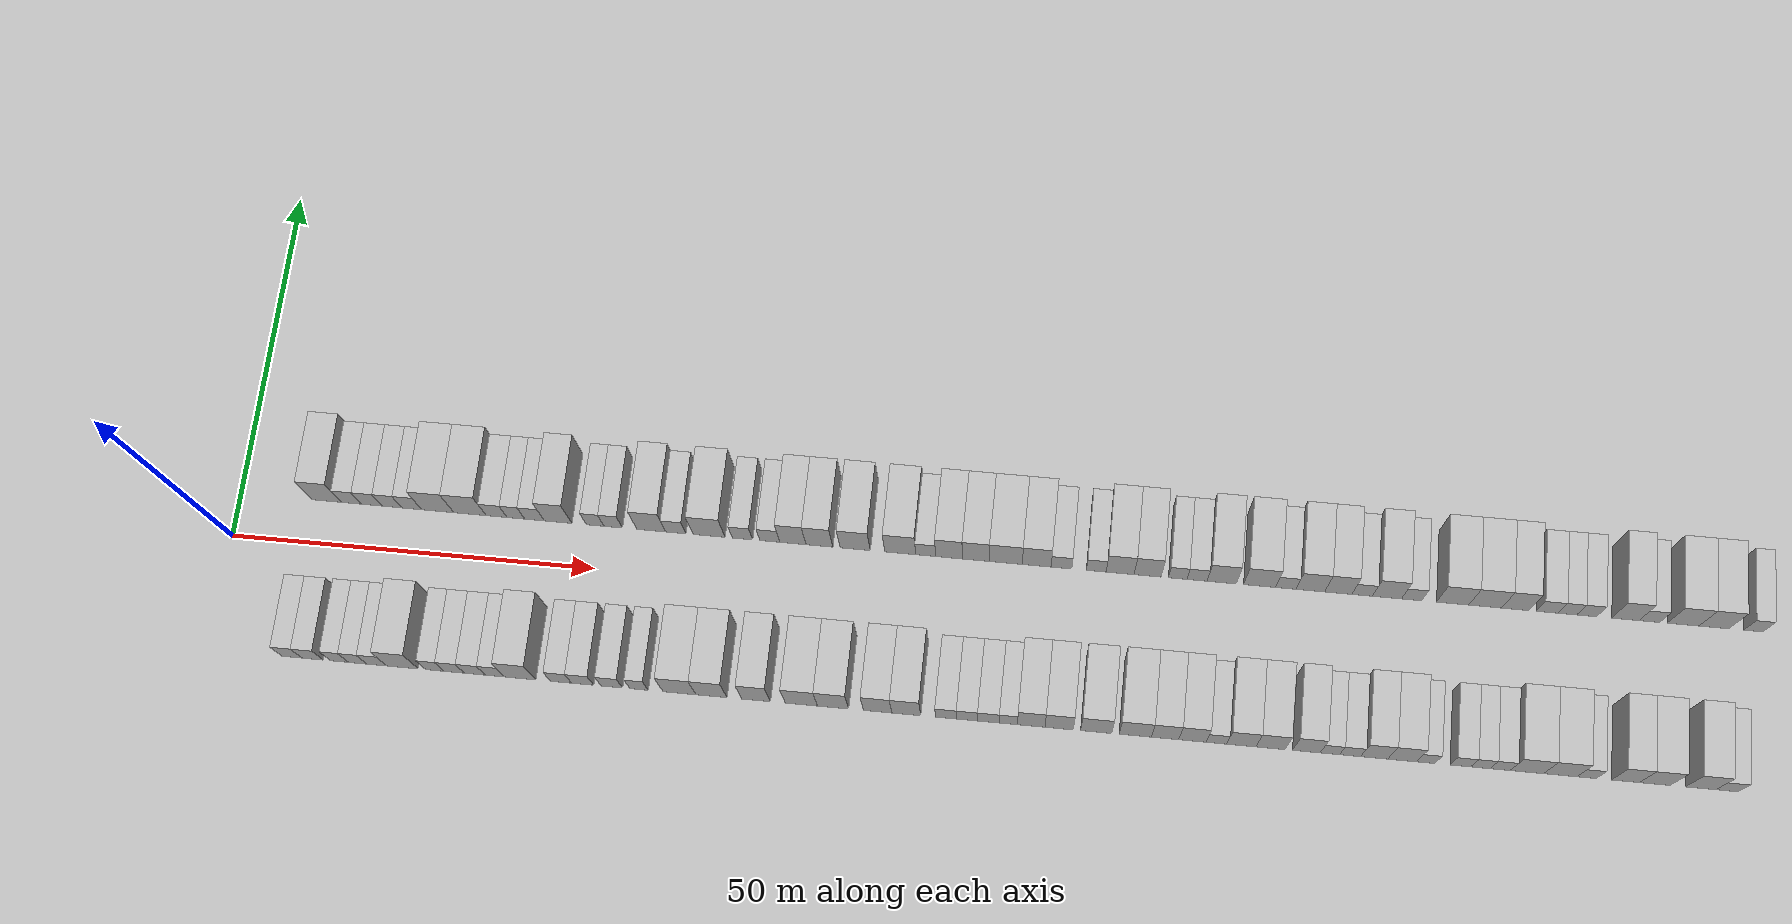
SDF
<?xml version="1.0" encoding="utf-8"?>

<sdf version="1.6">

   <world name="default">

      <gui fullscreen="0">

         <camera name="user_camera">

            <pose>-15 0 4.57585 0 0 0</pose>

            <view_controller>orbit</view_controller>

         </camera>

      </gui>

      <scene>

         <sky>

           <clouds>

             <speed>12</speed>

           </clouds>

         </sky>

         <ambient>0.4 0.4 0.4 1</ambient>

         <background>0.7 0.7 0.7 1</background>

         <shadows>1</shadows>

      </scene>

      <gravity>0 0 -9.8066</gravity>

      <magnetic_field>6e-06 2.3e-05 -4.2e-05</magnetic_field>

      <physics default="0" name="default_physics" type="ode">

         <ode>

            <solver>

               <type>quick</type>

               <iters>10</iters>

               <sor>1.0</sor>

               <use_dynamic_moi_rescaling>0</use_dynamic_moi_rescaling>

            </solver>

            <constraints>

               <cfm>0</cfm>

               <erp>0.2</erp>

               <contact_max_correcting_vel>100</contact_max_correcting_vel>

               <contact_surface_layer>0.001</contact_surface_layer>

            </constraints>

         </ode>

         <max_step_size>0.004</max_step_size>

         <real_time_factor>1</real_time_factor>

         <real_time_update_rate>250</real_time_update_rate>

      </physics>

      <light name="sun" type="directional">

         <cast_shadows>1</cast_shadows>

         <pose>0 0 10 0 0 0</pose>

         <diffuse>0.8 0.8 0.8 1</diffuse>

         <specular>0.2 0.2 0.2 1</specular>

         <attenuation>

            <range>1000</range>

            <constant>0.9</constant>

            <linear>0.01</linear>

            <quadratic>0.001</quadratic>

         </attenuation>

         <direction>-0.5 0.1 -0.9</direction>

      </light>

      <include>

         <name>ground_plane_1</name>

         <uri>model://HANNAS_ground_plane</uri>

         <pose>0 0 0  0 0 0</pose>

      </include>

      <include>

         <name>ground_plane_2</name>

         <uri>model://HANNAS_ground_plane</uri>

         <pose>100 0 0  0 0 0</pose>

      </include>

      <model name="building_1">

         <static>1</static>

         <pose frame="">12.0503 11.0000 0 0.000000 0.000000 1.570796</pose>

         <link name="link">

            <pose frame="">0 0 4.50 0 0 0</pose>

            <collision name="collision">

               <geometry>

                  <box>

                     <size>10.0000 4.1006 9.0000</size>

                  </box>

               </geometry>

               <max_contacts>10</max_contacts>

               <surface>

                  <contact>

                     <ode/>

                  </contact>

                  <bounce/>

                  <friction>

                     <torsional>

                        <ode/>

                     </torsional>

                     <ode/>

                  </friction>

               </surface>

            </collision>

            <visual name="visual">

               <cast_shadows>0</cast_shadows>

               <geometry>

                  <box>

                     <size>10.0000 4.1006 9.0000</size>

                  </box>

               </geometry>

               <material>

                  <script>

                     <uri>model://HANNAS_wall/materials/scripts</uri>

                     <uri>model://HANNAS_wall/materials/textures</uri>

                     <name>vrc/HANNAS_wall</name>

                  </script>

               </material>

            </visual>

            <self_collide>0</self_collide>

            <enable_wind>0</enable_wind>

            <kinematic>0</kinematic>

         </link>

      </model>

      <model name="building_2">

         <static>1</static>

         <pose frame="">15.4799 11.0000 0 0.000000 0.000000 1.570796</pose>

         <link name="link">

            <pose frame="">0 0 3.00 0 0 0</pose>

            <collision name="collision">

               <geometry>

                  <box>

                     <size>10.0000 2.7587 6.0000</size>

                  </box>

               </geometry>

               <max_contacts>10</max_contacts>

               <surface>

                  <contact>

                     <ode/>

                  </contact>

                  <bounce/>

                  <friction>

                     <torsional>

                        <ode/>

                     </torsional>

                     <ode/>

                  </friction>

               </surface>

            </collision>

            <visual name="visual">

               <cast_shadows>0</cast_shadows>

               <geometry>

                  <box>

                     <size>10.0000 2.7587 6.0000</size>

                  </box>

               </geometry>

               <material>

                  <script>

                     <uri>model://HANNAS_wall/materials/scripts</uri>

                     <uri>model://HANNAS_wall/materials/textures</uri>

                     <name>vrc/HANNAS_wall</name>

                  </script>

               </material>

            </visual>

            <self_collide>0</self_collide>

            <enable_wind>0</enable_wind>

            <kinematic>0</kinematic>

         </link>

      </model>

      <model name="building_3">

         <static>1</static>

         <pose frame="">18.2870 11.0000 0 0.000000 0.000000 1.570796</pose>

         <link name="link">

            <pose frame="">0 0 3.00 0 0 0</pose>

            <collision name="collision">

               <geometry>

                  <box>

                     <size>10.0000 2.8556 6.0000</size>

                  </box>

               </geometry>

               <max_contacts>10</max_contacts>

               <surface>

                  <contact>

                     <ode/>

                  </contact>

                  <bounce/>

                  <friction>

                     <torsional>

                        <ode/>

                     </torsional>

                     <ode/>

                  </friction>

               </surface>

            </collision>

            <visual name="visual">

               <cast_shadows>0</cast_shadows>

               <geometry>

                  <box>

                     <size>10.0000 2.8556 6.0000</size>

                  </box>

               </geometry>

               <material>

                  <script>

                     <uri>model://HANNAS_wall/materials/scripts</uri>

                     <uri>model://HANNAS_wall/materials/textures</uri>

                     <name>vrc/HANNAS_wall</name>

                  </script>

               </material>

            </visual>

            <self_collide>0</self_collide>

            <enable_wind>0</enable_wind>

            <kinematic>0</kinematic>

         </link>

      </model>

      <model name="building_4">

         <static>1</static>

         <pose frame="">21.0823 11.0000 0 0.000000 0.000000 1.570796</pose>

         <link name="link">

            <pose frame="">0 0 3.00 0 0 0</pose>

            <collision name="collision">

               <geometry>

                  <box>

                     <size>10.0000 2.7349 6.0000</size>

                  </box>

               </geometry>

               <max_contacts>10</max_contacts>

               <surface>

                  <contact>

                     <ode/>

                  </contact>

                  <bounce/>

                  <friction>

                     <torsional>

                        <ode/>

                     </torsional>

                     <ode/>

                  </friction>

               </surface>

            </collision>

            <visual name="visual">

               <cast_shadows>0</cast_shadows>

               <geometry>

                  <box>

                     <size>10.0000 2.7349 6.0000</size>

                  </box>

               </geometry>

               <material>

                  <script>

                     <uri>model://HANNAS_wall/materials/scripts</uri>

                     <uri>model://HANNAS_wall/materials/textures</uri>

                     <name>vrc/HANNAS_wall</name>

                  </script>

               </material>

            </visual>

            <self_collide>0</self_collide>

            <enable_wind>0</enable_wind>

            <kinematic>0</kinematic>

         </link>

      </model>

      <model name="building_5">

         <static>1</static>

         <pose frame="">23.8265 11.0000 0 0.000000 0.000000 1.570796</pose>

         <link name="link">

            <pose frame="">0 0 3.00 0 0 0</pose>

            <collision name="collision">

               <geometry>

                  <box>

                     <size>10.0000 2.7537 6.0000</size>

                  </box>

               </geometry>

               <max_contacts>10</max_contacts>

               <surface>

                  <contact>

                     <ode/>

                  </contact>

                  <bounce/>

                  <friction>

                     <torsional>

                        <ode/>

                     </torsional>

                     <ode/>

                  </friction>

               </surface>

            </collision>

            <visual name="visual">

               <cast_shadows>0</cast_shadows>

               <geometry>

                  <box>

                     <size>10.0000 2.7537 6.0000</size>

                  </box>

               </geometry>

               <material>

                  <script>

                     <uri>model://HANNAS_wall/materials/scripts</uri>

                     <uri>model://HANNAS_wall/materials/textures</uri>

                     <name>vrc/HANNAS_wall</name>

                  </script>

               </material>

            </visual>

            <self_collide>0</self_collide>

            <enable_wind>0</enable_wind>

            <kinematic>0</kinematic>

         </link>

      </model>

      <model name="building_6">

         <static>1</static>

         <pose frame="">27.4386 11.0000 0 0.000000 0.000000 1.570796</pose>

         <link name="link">

            <pose frame="">0 0 4.50 0 0 0</pose>

            <collision name="collision">

               <geometry>

                  <box>

                     <size>10.0000 4.4705 9.0000</size>

                  </box>

               </geometry>

               <max_contacts>10</max_contacts>

               <surface>

                  <contact>

                     <ode/>

                  </contact>

                  <bounce/>

                  <friction>

                     <torsional>

                        <ode/>

                     </torsional>

                     <ode/>

                  </friction>

               </surface>

            </collision>

            <visual name="visual">

               <cast_shadows>0</cast_shadows>

               <geometry>

                  <box>

                     <size>10.0000 4.4705 9.0000</size>

                  </box>

               </geometry>

               <material>

                  <script>

                     <uri>model://HANNAS_wall/materials/scripts</uri>

                     <uri>model://HANNAS_wall/materials/textures</uri>

                     <name>vrc/HANNAS_wall</name>

                  </script>

               </material>

            </visual>

            <self_collide>0</self_collide>

            <enable_wind>0</enable_wind>

            <kinematic>0</kinematic>

         </link>

      </model>

      <model name="building_7">

         <static>1</static>

         <pose frame="">31.9097 11.0000 0 0.000000 0.000000 1.570796</pose>

         <link name="link">

            <pose frame="">0 0 4.50 0 0 0</pose>

            <collision name="collision">

               <geometry>

                  <box>

                     <size>10.0000 4.4717 9.0000</size>

                  </box>

               </geometry>

               <max_contacts>10</max_contacts>

               <surface>

                  <contact>

                     <ode/>

                  </contact>

                  <bounce/>

                  <friction>

                     <torsional>

                        <ode/>

                     </torsional>

                     <ode/>

                  </friction>

               </surface>

            </collision>

            <visual name="visual">

               <cast_shadows>0</cast_shadows>

               <geometry>

                  <box>

                     <size>10.0000 4.4717 9.0000</size>

                  </box>

               </geometry>

               <material>

                  <script>

                     <uri>model://HANNAS_wall/materials/scripts</uri>

                     <uri>model://HANNAS_wall/materials/textures</uri>

                     <name>vrc/HANNAS_wall</name>

                  </script>

               </material>

            </visual>

            <self_collide>0</self_collide>

            <enable_wind>0</enable_wind>

            <kinematic>0</kinematic>

         </link>

      </model>

      <model name="building_8">

         <static>1</static>

         <pose frame="">35.5978 11.0000 0 0.000000 0.000000 1.570796</pose>

         <link name="link">

            <pose frame="">0 0 3.00 0 0 0</pose>

            <collision name="collision">

               <geometry>

                  <box>

                     <size>10.0000 2.9044 6.0000</size>

                  </box>

               </geometry>

               <max_contacts>10</max_contacts>

               <surface>

                  <contact>

                     <ode/>

                  </contact>

                  <bounce/>

                  <friction>

                     <torsional>

                        <ode/>

                     </torsional>

                     <ode/>

                  </friction>

               </surface>

            </collision>

            <visual name="visual">

               <cast_shadows>0</cast_shadows>

               <geometry>

                  <box>

                     <size>10.0000 2.9044 6.0000</size>

                  </box>

               </geometry>

               <material>

                  <script>

                     <uri>model://HANNAS_wall/materials/scripts</uri>

                     <uri>model://HANNAS_wall/materials/textures</uri>

                     <name>vrc/HANNAS_wall</name>

                  </script>

               </material>

            </visual>

            <self_collide>0</self_collide>

            <enable_wind>0</enable_wind>

            <kinematic>0</kinematic>

         </link>

      </model>

      <model name="building_9">

         <static>1</static>

         <pose frame="">38.2642 11.0000 0 0.000000 0.000000 1.570796</pose>

         <link name="link">

            <pose frame="">0 0 3.00 0 0 0</pose>

            <collision name="collision">

               <geometry>

                  <box>

                     <size>10.0000 2.4285 6.0000</size>

                  </box>

               </geometry>

               <max_contacts>10</max_contacts>

               <surface>

                  <contact>

                     <ode/>

                  </contact>

                  <bounce/>

                  <friction>

                     <torsional>

                        <ode/>

                     </torsional>

                     <ode/>

                  </friction>

               </surface>

            </collision>

            <visual name="visual">

               <cast_shadows>0</cast_shadows>

               <geometry>

                  <box>

                     <size>10.0000 2.4285 6.0000</size>

                  </box>

               </geometry>

               <material>

                  <script>

                     <uri>model://HANNAS_wall/materials/scripts</uri>

                     <uri>model://HANNAS_wall/materials/textures</uri>

                     <name>vrc/HANNAS_wall</name>

                  </script>

               </material>

            </visual>

            <self_collide>0</self_collide>

            <enable_wind>0</enable_wind>

            <kinematic>0</kinematic>

         </link>

      </model>

      <model name="building_10">

         <static>1</static>

         <pose frame="">40.8345 11.0000 0 0.000000 0.000000 1.570796</pose>

         <link name="link">

            <pose frame="">0 0 3.00 0 0 0</pose>

            <collision name="collision">

               <geometry>

                  <box>

                     <size>10.0000 2.7121 6.0000</size>

                  </box>

               </geometry>

               <max_contacts>10</max_contacts>

               <surface>

                  <contact>

                     <ode/>

                  </contact>

                  <bounce/>

                  <friction>

                     <torsional>

                        <ode/>

                     </torsional>

                     <ode/>

                  </friction>

               </surface>

            </collision>

            <visual name="visual">

               <cast_shadows>0</cast_shadows>

               <geometry>

                  <box>

                     <size>10.0000 2.7121 6.0000</size>

                  </box>

               </geometry>

               <material>

                  <script>

                     <uri>model://HANNAS_wall/materials/scripts</uri>

                     <uri>model://HANNAS_wall/materials/textures</uri>

                     <name>vrc/HANNAS_wall</name>

                  </script>

               </material>

            </visual>

            <self_collide>0</self_collide>

            <enable_wind>0</enable_wind>

            <kinematic>0</kinematic>

         </link>

      </model>

      <model name="building_11">

         <static>1</static>

         <pose frame="">44.0996 11.0000 0 0.000000 0.000000 1.570796</pose>

         <link name="link">

            <pose frame="">0 0 4.50 0 0 0</pose>

            <collision name="collision">

               <geometry>

                  <box>

                     <size>10.0000 3.8181 9.0000</size>

                  </box>

               </geometry>

               <max_contacts>10</max_contacts>

               <surface>

                  <contact>

                     <ode/>

                  </contact>

                  <bounce/>

                  <friction>

                     <torsional>

                        <ode/>

                     </torsional>

                     <ode/>

                  </friction>

               </surface>

            </collision>

            <visual name="visual">

               <cast_shadows>0</cast_shadows>

               <geometry>

                  <box>

                     <size>10.0000 3.8181 9.0000</size>

                  </box>

               </geometry>

               <material>

                  <script>

                     <uri>model://HANNAS_wall/materials/scripts</uri>

                     <uri>model://HANNAS_wall/materials/textures</uri>

                     <name>vrc/HANNAS_wall</name>

                  </script>

               </material>

            </visual>

            <self_collide>0</self_collide>

            <enable_wind>0</enable_wind>

            <kinematic>0</kinematic>

         </link>

      </model>

      <model name="building_12">

         <static>1</static>

         <pose frame="">49.2258 11.0000 0 0.000000 0.000000 1.570796</pose>

         <link name="link">

            <pose frame="">0 0 3.00 0 0 0</pose>

            <collision name="collision">

               <geometry>

                  <box>

                     <size>10.0000 2.4343 6.0000</size>

                  </box>

               </geometry>

               <max_contacts>10</max_contacts>

               <surface>

                  <contact>

                     <ode/>

                  </contact>

                  <bounce/>

                  <friction>

                     <torsional>

                        <ode/>

                     </torsional>

                     <ode/>

                  </friction>

               </surface>

            </collision>

            <visual name="visual">

               <cast_shadows>0</cast_shadows>

               <geometry>

                  <box>

                     <size>10.0000 2.4343 6.0000</size>

                  </box>

               </geometry>

               <material>

                  <script>

                     <uri>model://HANNAS_wall/materials/scripts</uri>

                     <uri>model://HANNAS_wall/materials/textures</uri>

                     <name>vrc/HANNAS_wall</name>

                  </script>

               </material>

            </visual>

            <self_collide>0</self_collide>

            <enable_wind>0</enable_wind>

            <kinematic>0</kinematic>

         </link>

      </model>

      <model name="building_13">

         <static>1</static>

         <pose frame="">51.7094 11.0000 0 0.000000 0.000000 1.570796</pose>

         <link name="link">

            <pose frame="">0 0 3.00 0 0 0</pose>

            <collision name="collision">

               <geometry>

                  <box>

                     <size>10.0000 2.5329 6.0000</size>

                  </box>

               </geometry>

               <max_contacts>10</max_contacts>

               <surface>

                  <contact>

                     <ode/>

                  </contact>

                  <bounce/>

                  <friction>

                     <torsional>

                        <ode/>

                     </torsional>

                     <ode/>

                  </friction>

               </surface>

            </collision>

            <visual name="visual">

               <cast_shadows>0</cast_shadows>

               <geometry>

                  <box>

                     <size>10.0000 2.5329 6.0000</size>

                  </box>

               </geometry>

               <material>

                  <script>

                     <uri>model://HANNAS_wall/materials/scripts</uri>

                     <uri>model://HANNAS_wall/materials/textures</uri>

                     <name>vrc/HANNAS_wall</name>

                  </script>

               </material>

            </visual>

            <self_collide>0</self_collide>

            <enable_wind>0</enable_wind>

            <kinematic>0</kinematic>

         </link>

      </model>

      <model name="building_14">

         <static>1</static>

         <pose frame="">56.9545 11.0000 0 0.000000 0.000000 1.570796</pose>

         <link name="link">

            <pose frame="">0 0 4.50 0 0 0</pose>

            <collision name="collision">

               <geometry>

                  <box>

                     <size>10.0000 3.9573 9.0000</size>

                  </box>

               </geometry>

               <max_contacts>10</max_contacts>

               <surface>

                  <contact>

                     <ode/>

                  </contact>

                  <bounce/>

                  <friction>

                     <torsional>

                        <ode/>

                     </torsional>

                     <ode/>

                  </friction>

               </surface>

            </collision>

            <visual name="visual">

               <cast_shadows>0</cast_shadows>

               <geometry>

                  <box>

                     <size>10.0000 3.9573 9.0000</size>

                  </box>

               </geometry>

               <material>

                  <script>

                     <uri>model://HANNAS_wall/materials/scripts</uri>

                     <uri>model://HANNAS_wall/materials/textures</uri>

                     <name>vrc/HANNAS_wall</name>

                  </script>

               </material>

            </visual>

            <self_collide>0</self_collide>

            <enable_wind>0</enable_wind>

            <kinematic>0</kinematic>

         </link>

      </model>

      <model name="building_15">

         <static>1</static>

         <pose frame="">60.3338 11.0000 0 0.000000 0.000000 1.570796</pose>

         <link name="link">

            <pose frame="">0 0 3.00 0 0 0</pose>

            <collision name="collision">

               <geometry>

                  <box>

                     <size>10.0000 2.8012 6.0000</size>

                  </box>

               </geometry>

               <max_contacts>10</max_contacts>

               <surface>

                  <contact>

                     <ode/>

                  </contact>

                  <bounce/>

                  <friction>

                     <torsional>

                        <ode/>

                     </torsional>

                     <ode/>

                  </friction>

               </surface>

            </collision>

            <visual name="visual">

               <cast_shadows>0</cast_shadows>

               <geometry>

                  <box>

                     <size>10.0000 2.8012 6.0000</size>

                  </box>

               </geometry>

               <material>

                  <script>

                     <uri>model://HANNAS_wall/materials/scripts</uri>

                     <uri>model://HANNAS_wall/materials/textures</uri>

                     <name>vrc/HANNAS_wall</name>

                  </script>

               </material>

            </visual>

            <self_collide>0</self_collide>

            <enable_wind>0</enable_wind>

            <kinematic>0</kinematic>

         </link>

      </model>

      <model name="building_16">

         <static>1</static>

         <pose frame="">64.9238 11.0000 0 0.000000 0.000000 1.570796</pose>

         <link name="link">

            <pose frame="">0 0 4.50 0 0 0</pose>

            <collision name="collision">

               <geometry>

                  <box>

                     <size>10.0000 4.3788 9.0000</size>

                  </box>

               </geometry>

               <max_contacts>10</max_contacts>

               <surface>

                  <contact>

                     <ode/>

                  </contact>

                  <bounce/>

                  <friction>

                     <torsional>

                        <ode/>

                     </torsional>

                     <ode/>

                  </friction>

               </surface>

            </collision>

            <visual name="visual">

               <cast_shadows>0</cast_shadows>

               <geometry>

                  <box>

                     <size>10.0000 4.3788 9.0000</size>

                  </box>

               </geometry>

               <material>

                  <script>

                     <uri>model://HANNAS_wall/materials/scripts</uri>

                     <uri>model://HANNAS_wall/materials/textures</uri>

                     <name>vrc/HANNAS_wall</name>

                  </script>

               </material>

            </visual>

            <self_collide>0</self_collide>

            <enable_wind>0</enable_wind>

            <kinematic>0</kinematic>

         </link>

      </model>

      <model name="building_17">

         <static>1</static>

         <pose frame="">69.5116 11.0000 0 0.000000 0.000000 1.570796</pose>

         <link name="link">

            <pose frame="">0 0 3.00 0 0 0</pose>

            <collision name="collision">

               <geometry>

                  <box>

                     <size>10.0000 2.7969 6.0000</size>

                  </box>

               </geometry>

               <max_contacts>10</max_contacts>

               <surface>

                  <contact>

                     <ode/>

                  </contact>

                  <bounce/>

                  <friction>

                     <torsional>

                        <ode/>

                     </torsional>

                     <ode/>

                  </friction>

               </surface>

            </collision>

            <visual name="visual">

               <cast_shadows>0</cast_shadows>

               <geometry>

                  <box>

                     <size>10.0000 2.7969 6.0000</size>

                  </box>

               </geometry>

               <material>

                  <script>

                     <uri>model://HANNAS_wall/materials/scripts</uri>

                     <uri>model://HANNAS_wall/materials/textures</uri>

                     <name>vrc/HANNAS_wall</name>

                  </script>

               </material>

            </visual>

            <self_collide>0</self_collide>

            <enable_wind>0</enable_wind>

            <kinematic>0</kinematic>

         </link>

      </model>

      <model name="building_18">

         <static>1</static>

         <pose frame="">73.2801 11.0000 0 0.000000 0.000000 1.570796</pose>

         <link name="link">

            <pose frame="">0 0 3.00 0 0 0</pose>

            <collision name="collision">

               <geometry>

                  <box>

                     <size>10.0000 2.7400 6.0000</size>

                  </box>

               </geometry>

               <max_contacts>10</max_contacts>

               <surface>

                  <contact>

                     <ode/>

                  </contact>

                  <bounce/>

                  <friction>

                     <torsional>

                        <ode/>

                     </torsional>

                     <ode/>

                  </friction>

               </surface>

            </collision>

            <visual name="visual">

               <cast_shadows>0</cast_shadows>

               <geometry>

                  <box>

                     <size>10.0000 2.7400 6.0000</size>

                  </box>

               </geometry>

               <material>

                  <script>

                     <uri>model://HANNAS_wall/materials/scripts</uri>

                     <uri>model://HANNAS_wall/materials/textures</uri>

                     <name>vrc/HANNAS_wall</name>

                  </script>

               </material>

            </visual>

            <self_collide>0</self_collide>

            <enable_wind>0</enable_wind>

            <kinematic>0</kinematic>

         </link>

      </model>

      <model name="building_19">

         <static>1</static>

         <pose frame="">76.4537 11.0000 0 0.000000 0.000000 1.570796</pose>

         <link name="link">

            <pose frame="">0 0 4.50 0 0 0</pose>

            <collision name="collision">

               <geometry>

                  <box>

                     <size>10.0000 3.6072 9.0000</size>

                  </box>

               </geometry>

               <max_contacts>10</max_contacts>

               <surface>

                  <contact>

                     <ode/>

                  </contact>

                  <bounce/>

                  <friction>

                     <torsional>

                        <ode/>

                     </torsional>

                     <ode/>

                  </friction>

               </surface>

            </collision>

            <visual name="visual">

               <cast_shadows>0</cast_shadows>

               <geometry>

                  <box>

                     <size>10.0000 3.6072 9.0000</size>

                  </box>

               </geometry>

               <material>

                  <script>

                     <uri>model://HANNAS_wall/materials/scripts</uri>

                     <uri>model://HANNAS_wall/materials/textures</uri>

                     <name>vrc/HANNAS_wall</name>

                  </script>

               </material>

            </visual>

            <self_collide>0</self_collide>

            <enable_wind>0</enable_wind>

            <kinematic>0</kinematic>

         </link>

      </model>

      <model name="building_20">

         <static>1</static>

         <pose frame="">80.0972 11.0000 0 0.000000 0.000000 1.570796</pose>

         <link name="link">

            <pose frame="">0 0 4.50 0 0 0</pose>

            <collision name="collision">

               <geometry>

                  <box>

                     <size>10.0000 3.6800 9.0000</size>

                  </box>

               </geometry>

               <max_contacts>10</max_contacts>

               <surface>

                  <contact>

                     <ode/>

                  </contact>

                  <bounce/>

                  <friction>

                     <torsional>

                        <ode/>

                     </torsional>

                     <ode/>

                  </friction>

               </surface>

            </collision>

            <visual name="visual">

               <cast_shadows>0</cast_shadows>

               <geometry>

                  <box>

                     <size>10.0000 3.6800 9.0000</size>

                  </box>

               </geometry>

               <material>

                  <script>

                     <uri>model://HANNAS_wall/materials/scripts</uri>

                     <uri>model://HANNAS_wall/materials/textures</uri>

                     <name>vrc/HANNAS_wall</name>

                  </script>

               </material>

            </visual>

            <self_collide>0</self_collide>

            <enable_wind>0</enable_wind>

            <kinematic>0</kinematic>

         </link>

      </model>

      <model name="building_21">

         <static>1</static>

         <pose frame="">85.0052 11.0000 0 0.000000 0.000000 1.570796</pose>

         <link name="link">

            <pose frame="">0 0 4.50 0 0 0</pose>

            <collision name="collision">

               <geometry>

                  <box>

                     <size>10.0000 4.1361 9.0000</size>

                  </box>

               </geometry>

               <max_contacts>10</max_contacts>

               <surface>

                  <contact>

                     <ode/>

                  </contact>

                  <bounce/>

                  <friction>

                     <torsional>

                        <ode/>

                     </torsional>

                     <ode/>

                  </friction>

               </surface>

            </collision>

            <visual name="visual">

               <cast_shadows>0</cast_shadows>

               <geometry>

                  <box>

                     <size>10.0000 4.1361 9.0000</size>

                  </box>

               </geometry>

               <material>

                  <script>

                     <uri>model://HANNAS_wall/materials/scripts</uri>

                     <uri>model://HANNAS_wall/materials/textures</uri>

                     <name>vrc/HANNAS_wall</name>

                  </script>

               </material>

            </visual>

            <self_collide>0</self_collide>

            <enable_wind>0</enable_wind>

            <kinematic>0</kinematic>

         </link>

      </model>

      <model name="building_22">

         <static>1</static>

         <pose frame="">91.2013 11.0000 0 0.000000 0.000000 1.570796</pose>

         <link name="link">

            <pose frame="">0 0 4.50 0 0 0</pose>

            <collision name="collision">

               <geometry>

                  <box>

                     <size>10.0000 4.2561 9.0000</size>

                  </box>

               </geometry>

               <max_contacts>10</max_contacts>

               <surface>

                  <contact>

                     <ode/>

                  </contact>

                  <bounce/>

                  <friction>

                     <torsional>

                        <ode/>

                     </torsional>

                     <ode/>

                  </friction>

               </surface>

            </collision>

            <visual name="visual">

               <cast_shadows>0</cast_shadows>

               <geometry>

                  <box>

                     <size>10.0000 4.2561 9.0000</size>

                  </box>

               </geometry>

               <material>

                  <script>

                     <uri>model://HANNAS_wall/materials/scripts</uri>

                     <uri>model://HANNAS_wall/materials/textures</uri>

                     <name>vrc/HANNAS_wall</name>

                  </script>

               </material>

            </visual>

            <self_collide>0</self_collide>

            <enable_wind>0</enable_wind>

            <kinematic>0</kinematic>

         </link>

      </model>

      <model name="building_23">

         <static>1</static>

         <pose frame="">94.6936 11.0000 0 0.000000 0.000000 1.570796</pose>

         <link name="link">

            <pose frame="">0 0 3.00 0 0 0</pose>

            <collision name="collision">

               <geometry>

                  <box>

                     <size>10.0000 2.7285 6.0000</size>

                  </box>

               </geometry>

               <max_contacts>10</max_contacts>

               <surface>

                  <contact>

                     <ode/>

                  </contact>

                  <bounce/>

                  <friction>

                     <torsional>

                        <ode/>

                     </torsional>

                     <ode/>

                  </friction>

               </surface>

            </collision>

            <visual name="visual">

               <cast_shadows>0</cast_shadows>

               <geometry>

                  <box>

                     <size>10.0000 2.7285 6.0000</size>

                  </box>

               </geometry>

               <material>

                  <script>

                     <uri>model://HANNAS_wall/materials/scripts</uri>

                     <uri>model://HANNAS_wall/materials/textures</uri>

                     <name>vrc/HANNAS_wall</name>

                  </script>

               </material>

            </visual>

            <self_collide>0</self_collide>

            <enable_wind>0</enable_wind>

            <kinematic>0</kinematic>

         </link>

      </model>

      <model name="building_24">

         <static>1</static>

         <pose frame="">97.8919 11.0000 0 0.000000 0.000000 1.570796</pose>

         <link name="link">

            <pose frame="">0 0 4.50 0 0 0</pose>

            <collision name="collision">

               <geometry>

                  <box>

                     <size>10.0000 3.6681 9.0000</size>

                  </box>

               </geometry>

               <max_contacts>10</max_contacts>

               <surface>

                  <contact>

                     <ode/>

                  </contact>

                  <bounce/>

                  <friction>

                     <torsional>

                        <ode/>

                     </torsional>

                     <ode/>

                  </friction>

               </surface>

            </collision>

            <visual name="visual">

               <cast_shadows>0</cast_shadows>

               <geometry>

                  <box>

                     <size>10.0000 3.6681 9.0000</size>

                  </box>

               </geometry>

               <material>

                  <script>

                     <uri>model://HANNAS_wall/materials/scripts</uri>

                     <uri>model://HANNAS_wall/materials/textures</uri>

                     <name>vrc/HANNAS_wall</name>

                  </script>

               </material>

            </visual>

            <self_collide>0</self_collide>

            <enable_wind>0</enable_wind>

            <kinematic>0</kinematic>

         </link>

      </model>

      <model name="building_25">

         <static>1</static>

         <pose frame="">101.5623 11.0000 0 0.000000 0.000000 1.570796</pose>

         <link name="link">

            <pose frame="">0 0 4.50 0 0 0</pose>

            <collision name="collision">

               <geometry>

                  <box>

                     <size>10.0000 3.6725 9.0000</size>

                  </box>

               </geometry>

               <max_contacts>10</max_contacts>

               <surface>

                  <contact>

                     <ode/>

                  </contact>

                  <bounce/>

                  <friction>

                     <torsional>

                        <ode/>

                     </torsional>

                     <ode/>

                  </friction>

               </surface>

            </collision>

            <visual name="visual">

               <cast_shadows>0</cast_shadows>

               <geometry>

                  <box>

                     <size>10.0000 3.6725 9.0000</size>

                  </box>

               </geometry>

               <material>

                  <script>

                     <uri>model://HANNAS_wall/materials/scripts</uri>

                     <uri>model://HANNAS_wall/materials/textures</uri>

                     <name>vrc/HANNAS_wall</name>

                  </script>

               </material>

            </visual>

            <self_collide>0</self_collide>

            <enable_wind>0</enable_wind>

            <kinematic>0</kinematic>

         </link>

      </model>

      <model name="building_26">

         <static>1</static>

         <pose frame="">105.6455 11.0000 0 0.000000 0.000000 1.570796</pose>

         <link name="link">

            <pose frame="">0 0 4.50 0 0 0</pose>

            <collision name="collision">

               <geometry>

                  <box>

                     <size>10.0000 4.4938 9.0000</size>

                  </box>

               </geometry>

               <max_contacts>10</max_contacts>

               <surface>

                  <contact>

                     <ode/>

                  </contact>

                  <bounce/>

                  <friction>

                     <torsional>

                        <ode/>

                     </torsional>

                     <ode/>

                  </friction>

               </surface>

            </collision>

            <visual name="visual">

               <cast_shadows>0</cast_shadows>

               <geometry>

                  <box>

                     <size>10.0000 4.4938 9.0000</size>

                  </box>

               </geometry>

               <material>

                  <script>

                     <uri>model://HANNAS_wall/materials/scripts</uri>

                     <uri>model://HANNAS_wall/materials/textures</uri>

                     <name>vrc/HANNAS_wall</name>

                  </script>

               </material>

            </visual>

            <self_collide>0</self_collide>

            <enable_wind>0</enable_wind>

            <kinematic>0</kinematic>

         </link>

      </model>

      <model name="building_27">

         <static>1</static>

         <pose frame="">109.8516 11.0000 0 0.000000 0.000000 1.570796</pose>

         <link name="link">

            <pose frame="">0 0 4.50 0 0 0</pose>

            <collision name="collision">

               <geometry>

                  <box>

                     <size>10.0000 3.9184 9.0000</size>

                  </box>

               </geometry>

               <max_contacts>10</max_contacts>

               <surface>

                  <contact>

                     <ode/>

                  </contact>

                  <bounce/>

                  <friction>

                     <torsional>

                        <ode/>

                     </torsional>

                     <ode/>

                  </friction>

               </surface>

            </collision>

            <visual name="visual">

               <cast_shadows>0</cast_shadows>

               <geometry>

                  <box>

                     <size>10.0000 3.9184 9.0000</size>

                  </box>

               </geometry>

               <material>

                  <script>

                     <uri>model://HANNAS_wall/materials/scripts</uri>

                     <uri>model://HANNAS_wall/materials/textures</uri>

                     <name>vrc/HANNAS_wall</name>

                  </script>

               </material>

            </visual>

            <self_collide>0</self_collide>

            <enable_wind>0</enable_wind>

            <kinematic>0</kinematic>

         </link>

      </model>

      <model name="building_28">

         <static>1</static>

         <pose frame="">113.2139 11.0000 0 0.000000 0.000000 1.570796</pose>

         <link name="link">

            <pose frame="">0 0 3.00 0 0 0</pose>

            <collision name="collision">

               <geometry>

                  <box>

                     <size>10.0000 2.8062 6.0000</size>

                  </box>

               </geometry>

               <max_contacts>10</max_contacts>

               <surface>

                  <contact>

                     <ode/>

                  </contact>

                  <bounce/>

                  <friction>

                     <torsional>

                        <ode/>

                     </torsional>

                     <ode/>

                  </friction>

               </surface>

            </collision>

            <visual name="visual">

               <cast_shadows>0</cast_shadows>

               <geometry>

                  <box>

                     <size>10.0000 2.8062 6.0000</size>

                  </box>

               </geometry>

               <material>

                  <script>

                     <uri>model://HANNAS_wall/materials/scripts</uri>

                     <uri>model://HANNAS_wall/materials/textures</uri>

                     <name>vrc/HANNAS_wall</name>

                  </script>

               </material>

            </visual>

            <self_collide>0</self_collide>

            <enable_wind>0</enable_wind>

            <kinematic>0</kinematic>

         </link>

      </model>

      <model name="building_29">

         <static>1</static>

         <pose frame="">117.9558 11.0000 0 0.000000 0.000000 1.570796</pose>

         <link name="link">

            <pose frame="">0 0 3.00 0 0 0</pose>

            <collision name="collision">

               <geometry>

                  <box>

                     <size>10.0000 2.6777 6.0000</size>

                  </box>

               </geometry>

               <max_contacts>10</max_contacts>

               <surface>

                  <contact>

                     <ode/>

                  </contact>

                  <bounce/>

                  <friction>

                     <torsional>

                        <ode/>

                     </torsional>

                     <ode/>

                  </friction>

               </surface>

            </collision>

            <visual name="visual">

               <cast_shadows>0</cast_shadows>

               <geometry>

                  <box>

                     <size>10.0000 2.6777 6.0000</size>

                  </box>

               </geometry>

               <material>

                  <script>

                     <uri>model://HANNAS_wall/materials/scripts</uri>

                     <uri>model://HANNAS_wall/materials/textures</uri>

                     <name>vrc/HANNAS_wall</name>

                  </script>

               </material>

            </visual>

            <self_collide>0</self_collide>

            <enable_wind>0</enable_wind>

            <kinematic>0</kinematic>

         </link>

      </model>

      <model name="building_30">

         <static>1</static>

         <pose frame="">121.2060 11.0000 0 0.000000 0.000000 1.570796</pose>

         <link name="link">

            <pose frame="">0 0 4.50 0 0 0</pose>

            <collision name="collision">

               <geometry>

                  <box>

                     <size>10.0000 3.8227 9.0000</size>

                  </box>

               </geometry>

               <max_contacts>10</max_contacts>

               <surface>

                  <contact>

                     <ode/>

                  </contact>

                  <bounce/>

                  <friction>

                     <torsional>

                        <ode/>

                     </torsional>

                     <ode/>

                  </friction>

               </surface>

            </collision>

            <visual name="visual">

               <cast_shadows>0</cast_shadows>

               <geometry>

                  <box>

                     <size>10.0000 3.8227 9.0000</size>

                  </box>

               </geometry>

               <material>

                  <script>

                     <uri>model://HANNAS_wall/materials/scripts</uri>

                     <uri>model://HANNAS_wall/materials/textures</uri>

                     <name>vrc/HANNAS_wall</name>

                  </script>

               </material>

            </visual>

            <self_collide>0</self_collide>

            <enable_wind>0</enable_wind>

            <kinematic>0</kinematic>

         </link>

      </model>

      <model name="building_31">

         <static>1</static>

         <pose frame="">124.9539 11.0000 0 0.000000 0.000000 1.570796</pose>

         <link name="link">

            <pose frame="">0 0 4.50 0 0 0</pose>

            <collision name="collision">

               <geometry>

                  <box>

                     <size>10.0000 3.6730 9.0000</size>

                  </box>

               </geometry>

               <max_contacts>10</max_contacts>

               <surface>

                  <contact>

                     <ode/>

                  </contact>

                  <bounce/>

                  <friction>

                     <torsional>

                        <ode/>

                     </torsional>

                     <ode/>

                  </friction>

               </surface>

            </collision>

            <visual name="visual">

               <cast_shadows>0</cast_shadows>

               <geometry>

                  <box>

                     <size>10.0000 3.6730 9.0000</size>

                  </box>

               </geometry>

               <material>

                  <script>

                     <uri>model://HANNAS_wall/materials/scripts</uri>

                     <uri>model://HANNAS_wall/materials/textures</uri>

                     <name>vrc/HANNAS_wall</name>

                  </script>

               </material>

            </visual>

            <self_collide>0</self_collide>

            <enable_wind>0</enable_wind>

            <kinematic>0</kinematic>

         </link>

      </model>

      <model name="building_32">

         <static>1</static>

         <pose frame="">129.0474 11.0000 0 0.000000 0.000000 1.570796</pose>

         <link name="link">

            <pose frame="">0 0 3.00 0 0 0</pose>

            <collision name="collision">

               <geometry>

                  <box>

                     <size>10.0000 2.5141 6.0000</size>

                  </box>

               </geometry>

               <max_contacts>10</max_contacts>

               <surface>

                  <contact>

                     <ode/>

                  </contact>

                  <bounce/>

                  <friction>

                     <torsional>

                        <ode/>

                     </torsional>

                     <ode/>

                  </friction>

               </surface>

            </collision>

            <visual name="visual">

               <cast_shadows>0</cast_shadows>

               <geometry>

                  <box>

                     <size>10.0000 2.5141 6.0000</size>

                  </box>

               </geometry>

               <material>

                  <script>

                     <uri>model://HANNAS_wall/materials/scripts</uri>

                     <uri>model://HANNAS_wall/materials/textures</uri>

                     <name>vrc/HANNAS_wall</name>

                  </script>

               </material>

            </visual>

            <self_collide>0</self_collide>

            <enable_wind>0</enable_wind>

            <kinematic>0</kinematic>

         </link>

      </model>

      <model name="building_33">

         <static>1</static>

         <pose frame="">131.6731 11.0000 0 0.000000 0.000000 1.570796</pose>

         <link name="link">

            <pose frame="">0 0 3.00 0 0 0</pose>

            <collision name="collision">

               <geometry>

                  <box>

                     <size>10.0000 2.7373 6.0000</size>

                  </box>

               </geometry>

               <max_contacts>10</max_contacts>

               <surface>

                  <contact>

                     <ode/>

                  </contact>

                  <bounce/>

                  <friction>

                     <torsional>

                        <ode/>

                     </torsional>

                     <ode/>

                  </friction>

               </surface>

            </collision>

            <visual name="visual">

               <cast_shadows>0</cast_shadows>

               <geometry>

                  <box>

                     <size>10.0000 2.7373 6.0000</size>

                  </box>

               </geometry>

               <material>

                  <script>

                     <uri>model://HANNAS_wall/materials/scripts</uri>

                     <uri>model://HANNAS_wall/materials/textures</uri>

                     <name>vrc/HANNAS_wall</name>

                  </script>

               </material>

            </visual>

            <self_collide>0</self_collide>

            <enable_wind>0</enable_wind>

            <kinematic>0</kinematic>

         </link>

      </model>

      <model name="building_34">

         <static>1</static>

         <pose frame="">135.0254 11.0000 0 0.000000 0.000000 1.570796</pose>

         <link name="link">

            <pose frame="">0 0 4.50 0 0 0</pose>

            <collision name="collision">

               <geometry>

                  <box>

                     <size>10.0000 3.9672 9.0000</size>

                  </box>

               </geometry>

               <max_contacts>10</max_contacts>

               <surface>

                  <contact>

                     <ode/>

                  </contact>

                  <bounce/>

                  <friction>

                     <torsional>

                        <ode/>

                     </torsional>

                     <ode/>

                  </friction>

               </surface>

            </collision>

            <visual name="visual">

               <cast_shadows>0</cast_shadows>

               <geometry>

                  <box>

                     <size>10.0000 3.9672 9.0000</size>

                  </box>

               </geometry>

               <material>

                  <script>

                     <uri>model://HANNAS_wall/materials/scripts</uri>

                     <uri>model://HANNAS_wall/materials/textures</uri>

                     <name>vrc/HANNAS_wall</name>

                  </script>

               </material>

            </visual>

            <self_collide>0</self_collide>

            <enable_wind>0</enable_wind>

            <kinematic>0</kinematic>

         </link>

      </model>

      <model name="building_35">

         <static>1</static>

         <pose frame="">140.1852 11.0000 0 0.000000 0.000000 1.570796</pose>

         <link name="link">

            <pose frame="">0 0 4.50 0 0 0</pose>

            <collision name="collision">

               <geometry>

                  <box>

                     <size>10.0000 4.3525 9.0000</size>

                  </box>

               </geometry>

               <max_contacts>10</max_contacts>

               <surface>

                  <contact>

                     <ode/>

                  </contact>

                  <bounce/>

                  <friction>

                     <torsional>

                        <ode/>

                     </torsional>

                     <ode/>

                  </friction>

               </surface>

            </collision>

            <visual name="visual">

               <cast_shadows>0</cast_shadows>

               <geometry>

                  <box>

                     <size>10.0000 4.3525 9.0000</size>

                  </box>

               </geometry>

               <material>

                  <script>

                     <uri>model://HANNAS_wall/materials/scripts</uri>

                     <uri>model://HANNAS_wall/materials/textures</uri>

                     <name>vrc/HANNAS_wall</name>

                  </script>

               </material>

            </visual>

            <self_collide>0</self_collide>

            <enable_wind>0</enable_wind>

            <kinematic>0</kinematic>

         </link>

      </model>

      <model name="building_36">

         <static>1</static>

         <pose frame="">143.7481 11.0000 0 0.000000 0.000000 1.570796</pose>

         <link name="link">

            <pose frame="">0 0 3.00 0 0 0</pose>

            <collision name="collision">

               <geometry>

                  <box>

                     <size>10.0000 2.7732 6.0000</size>

                  </box>

               </geometry>

               <max_contacts>10</max_contacts>

               <surface>

                  <contact>

                     <ode/>

                  </contact>

                  <bounce/>

                  <friction>

                     <torsional>

                        <ode/>

                     </torsional>

                     <ode/>

                  </friction>

               </surface>

            </collision>

            <visual name="visual">

               <cast_shadows>0</cast_shadows>

               <geometry>

                  <box>

                     <size>10.0000 2.7732 6.0000</size>

                  </box>

               </geometry>

               <material>

                  <script>

                     <uri>model://HANNAS_wall/materials/scripts</uri>

                     <uri>model://HANNAS_wall/materials/textures</uri>

                     <name>vrc/HANNAS_wall</name>

                  </script>

               </material>

            </visual>

            <self_collide>0</self_collide>

            <enable_wind>0</enable_wind>

            <kinematic>0</kinematic>

         </link>

      </model>

      <model name="building_37">

         <static>1</static>

         <pose frame="">147.0758 11.0000 0 0.000000 0.000000 1.570796</pose>

         <link name="link">

            <pose frame="">0 0 4.50 0 0 0</pose>

            <collision name="collision">

               <geometry>

                  <box>

                     <size>10.0000 3.8821 9.0000</size>

                  </box>

               </geometry>

               <max_contacts>10</max_contacts>

               <surface>

                  <contact>

                     <ode/>

                  </contact>

                  <bounce/>

                  <friction>

                     <torsional>

                        <ode/>

                     </torsional>

                     <ode/>

                  </friction>

               </surface>

            </collision>

            <visual name="visual">

               <cast_shadows>0</cast_shadows>

               <geometry>

                  <box>

                     <size>10.0000 3.8821 9.0000</size>

                  </box>

               </geometry>

               <material>

                  <script>

                     <uri>model://HANNAS_wall/materials/scripts</uri>

                     <uri>model://HANNAS_wall/materials/textures</uri>

                     <name>vrc/HANNAS_wall</name>

                  </script>

               </material>

            </visual>

            <self_collide>0</self_collide>

            <enable_wind>0</enable_wind>

            <kinematic>0</kinematic>

         </link>

      </model>

      <model name="building_38">

         <static>1</static>

         <pose frame="">150.8622 11.0000 0 0.000000 0.000000 1.570796</pose>

         <link name="link">

            <pose frame="">0 0 4.50 0 0 0</pose>

            <collision name="collision">

               <geometry>

                  <box>

                     <size>10.0000 3.6908 9.0000</size>

                  </box>

               </geometry>

               <max_contacts>10</max_contacts>

               <surface>

                  <contact>

                     <ode/>

                  </contact>

                  <bounce/>

                  <friction>

                     <torsional>

                        <ode/>

                     </torsional>

                     <ode/>

                  </friction>

               </surface>

            </collision>

            <visual name="visual">

               <cast_shadows>0</cast_shadows>

               <geometry>

                  <box>

                     <size>10.0000 3.6908 9.0000</size>

                  </box>

               </geometry>

               <material>

                  <script>

                     <uri>model://HANNAS_wall/materials/scripts</uri>

                     <uri>model://HANNAS_wall/materials/textures</uri>

                     <name>vrc/HANNAS_wall</name>

                  </script>

               </material>

            </visual>

            <self_collide>0</self_collide>

            <enable_wind>0</enable_wind>

            <kinematic>0</kinematic>

         </link>

      </model>

      <model name="building_39">

         <static>1</static>

         <pose frame="">154.0975 11.0000 0 0.000000 0.000000 1.570796</pose>

         <link name="link">

            <pose frame="">0 0 3.00 0 0 0</pose>

            <collision name="collision">

               <geometry>

                  <box>

                     <size>10.0000 2.7798 6.0000</size>

                  </box>

               </geometry>

               <max_contacts>10</max_contacts>

               <surface>

                  <contact>

                     <ode/>

                  </contact>

                  <bounce/>

                  <friction>

                     <torsional>

                        <ode/>

                     </torsional>

                     <ode/>

                  </friction>

               </surface>

            </collision>

            <visual name="visual">

               <cast_shadows>0</cast_shadows>

               <geometry>

                  <box>

                     <size>10.0000 2.7798 6.0000</size>

                  </box>

               </geometry>

               <material>

                  <script>

                     <uri>model://HANNAS_wall/materials/scripts</uri>

                     <uri>model://HANNAS_wall/materials/textures</uri>

                     <name>vrc/HANNAS_wall</name>

                  </script>

               </material>

            </visual>

            <self_collide>0</self_collide>

            <enable_wind>0</enable_wind>

            <kinematic>0</kinematic>

         </link>

      </model>

      <model name="building_40">

         <static>1</static>

         <pose frame="">157.4542 11.0000 0 0.000000 0.000000 1.570796</pose>

         <link name="link">

            <pose frame="">0 0 4.50 0 0 0</pose>

            <collision name="collision">

               <geometry>

                  <box>

                     <size>10.0000 3.9337 9.0000</size>

                  </box>

               </geometry>

               <max_contacts>10</max_contacts>

               <surface>

                  <contact>

                     <ode/>

                  </contact>

                  <bounce/>

                  <friction>

                     <torsional>

                        <ode/>

                     </torsional>

                     <ode/>

                  </friction>

               </surface>

            </collision>

            <visual name="visual">

               <cast_shadows>0</cast_shadows>

               <geometry>

                  <box>

                     <size>10.0000 3.9337 9.0000</size>

                  </box>

               </geometry>

               <material>

                  <script>

                     <uri>model://HANNAS_wall/materials/scripts</uri>

                     <uri>model://HANNAS_wall/materials/textures</uri>

                     <name>vrc/HANNAS_wall</name>

                  </script>

               </material>

            </visual>

            <self_collide>0</self_collide>

            <enable_wind>0</enable_wind>

            <kinematic>0</kinematic>

         </link>

      </model>

      <model name="building_41">

         <static>1</static>

         <pose frame="">160.7927 11.0000 0 0.000000 0.000000 1.570796</pose>

         <link name="link">

            <pose frame="">0 0 3.00 0 0 0</pose>

            <collision name="collision">

               <geometry>

                  <box>

                     <size>10.0000 2.7434 6.0000</size>

                  </box>

               </geometry>

               <max_contacts>10</max_contacts>

               <surface>

                  <contact>

                     <ode/>

                  </contact>

                  <bounce/>

                  <friction>

                     <torsional>

                        <ode/>

                     </torsional>

                     <ode/>

                  </friction>

               </surface>

            </collision>

            <visual name="visual">

               <cast_shadows>0</cast_shadows>

               <geometry>

                  <box>

                     <size>10.0000 2.7434 6.0000</size>

                  </box>

               </geometry>

               <material>

                  <script>

                     <uri>model://HANNAS_wall/materials/scripts</uri>

                     <uri>model://HANNAS_wall/materials/textures</uri>

                     <name>vrc/HANNAS_wall</name>

                  </script>

               </material>

            </visual>

            <self_collide>0</self_collide>

            <enable_wind>0</enable_wind>

            <kinematic>0</kinematic>

         </link>

      </model>

      <model name="building_42">

         <static>1</static>

         <pose frame="">166.3499 11.0000 0 0.000000 0.000000 1.570796</pose>

         <link name="link">

            <pose frame="">0 0 4.50 0 0 0</pose>

            <collision name="collision">

               <geometry>

                  <box>

                     <size>10.0000 4.3709 9.0000</size>

                  </box>

               </geometry>

               <max_contacts>10</max_contacts>

               <surface>

                  <contact>

                     <ode/>

                  </contact>

                  <bounce/>

                  <friction>

                     <torsional>

                        <ode/>

                     </torsional>

                     <ode/>

                  </friction>

               </surface>

            </collision>

            <visual name="visual">

               <cast_shadows>0</cast_shadows>

               <geometry>

                  <box>

                     <size>10.0000 4.3709 9.0000</size>

                  </box>

               </geometry>

               <material>

                  <script>

                     <uri>model://HANNAS_wall/materials/scripts</uri>

                     <uri>model://HANNAS_wall/materials/textures</uri>

                     <name>vrc/HANNAS_wall</name>

                  </script>

               </material>

            </visual>

            <self_collide>0</self_collide>

            <enable_wind>0</enable_wind>

            <kinematic>0</kinematic>

         </link>

      </model>

      <model name="building_43">

         <static>1</static>

         <pose frame="">170.7616 11.0000 0 0.000000 0.000000 1.570796</pose>

         <link name="link">

            <pose frame="">0 0 4.50 0 0 0</pose>

            <collision name="collision">

               <geometry>

                  <box>

                     <size>10.0000 4.4524 9.0000</size>

                  </box>

               </geometry>

               <max_contacts>10</max_contacts>

               <surface>

                  <contact>

                     <ode/>

                  </contact>

                  <bounce/>

                  <friction>

                     <torsional>

                        <ode/>

                     </torsional>

                     <ode/>

                  </friction>

               </surface>

            </collision>

            <visual name="visual">

               <cast_shadows>0</cast_shadows>

               <geometry>

                  <box>

                     <size>10.0000 4.4524 9.0000</size>

                  </box>

               </geometry>

               <material>

                  <script>

                     <uri>model://HANNAS_wall/materials/scripts</uri>

                     <uri>model://HANNAS_wall/materials/textures</uri>

                     <name>vrc/HANNAS_wall</name>

                  </script>

               </material>

            </visual>

            <self_collide>0</self_collide>

            <enable_wind>0</enable_wind>

            <kinematic>0</kinematic>

         </link>

      </model>

      <model name="building_44">

         <static>1</static>

         <pose frame="">174.8276 11.0000 0 0.000000 0.000000 1.570796</pose>

         <link name="link">

            <pose frame="">0 0 4.50 0 0 0</pose>

            <collision name="collision">

               <geometry>

                  <box>

                     <size>10.0000 3.6796 9.0000</size>

                  </box>

               </geometry>

               <max_contacts>10</max_contacts>

               <surface>

                  <contact>

                     <ode/>

                  </contact>

                  <bounce/>

                  <friction>

                     <torsional>

                        <ode/>

                     </torsional>

                     <ode/>

                  </friction>

               </surface>

            </collision>

            <visual name="visual">

               <cast_shadows>0</cast_shadows>

               <geometry>

                  <box>

                     <size>10.0000 3.6796 9.0000</size>

                  </box>

               </geometry>

               <material>

                  <script>

                     <uri>model://HANNAS_wall/materials/scripts</uri>

                     <uri>model://HANNAS_wall/materials/textures</uri>

                     <name>vrc/HANNAS_wall</name>

                  </script>

               </material>

            </visual>

            <self_collide>0</self_collide>

            <enable_wind>0</enable_wind>

            <kinematic>0</kinematic>

         </link>

      </model>

      <model name="building_45">

         <static>1</static>

         <pose frame="">179.1522 11.0000 0 0.000000 0.000000 1.570796</pose>

         <link name="link">

            <pose frame="">0 0 3.00 0 0 0</pose>

            <collision name="collision">

               <geometry>

                  <box>

                     <size>10.0000 2.9696 6.0000</size>

                  </box>

               </geometry>

               <max_contacts>10</max_contacts>

               <surface>

                  <contact>

                     <ode/>

                  </contact>

                  <bounce/>

                  <friction>

                     <torsional>

                        <ode/>

                     </torsional>

                     <ode/>

                  </friction>

               </surface>

            </collision>

            <visual name="visual">

               <cast_shadows>0</cast_shadows>

               <geometry>

                  <box>

                     <size>10.0000 2.9696 6.0000</size>

                  </box>

               </geometry>

               <material>

                  <script>

                     <uri>model://HANNAS_wall/materials/scripts</uri>

                     <uri>model://HANNAS_wall/materials/textures</uri>

                     <name>vrc/HANNAS_wall</name>

                  </script>

               </material>

            </visual>

            <self_collide>0</self_collide>

            <enable_wind>0</enable_wind>

            <kinematic>0</kinematic>

         </link>

      </model>

      <model name="building_46">

         <static>1</static>

         <pose frame="">181.8782 11.0000 0 0.000000 0.000000 1.570796</pose>

         <link name="link">

            <pose frame="">0 0 3.00 0 0 0</pose>

            <collision name="collision">

               <geometry>

                  <box>

                     <size>10.0000 2.4825 6.0000</size>

                  </box>

               </geometry>

               <max_contacts>10</max_contacts>

               <surface>

                  <contact>

                     <ode/>

                  </contact>

                  <bounce/>

                  <friction>

                     <torsional>

                        <ode/>

                     </torsional>

                     <ode/>

                  </friction>

               </surface>

            </collision>

            <visual name="visual">

               <cast_shadows>0</cast_shadows>

               <geometry>

                  <box>

                     <size>10.0000 2.4825 6.0000</size>

                  </box>

               </geometry>

               <material>

                  <script>

                     <uri>model://HANNAS_wall/materials/scripts</uri>

                     <uri>model://HANNAS_wall/materials/textures</uri>

                     <name>vrc/HANNAS_wall</name>

                  </script>

               </material>

            </visual>

            <self_collide>0</self_collide>

            <enable_wind>0</enable_wind>

            <kinematic>0</kinematic>

         </link>

      </model>

      <model name="building_47">

         <static>1</static>

         <pose frame="">184.4671 11.0000 0 0.000000 0.000000 1.570796</pose>

         <link name="link">

            <pose frame="">0 0 3.00 0 0 0</pose>

            <collision name="collision">

               <geometry>

                  <box>

                     <size>10.0000 2.6953 6.0000</size>

                  </box>

               </geometry>

               <max_contacts>10</max_contacts>

               <surface>

                  <contact>

                     <ode/>

                  </contact>

                  <bounce/>

                  <friction>

                     <torsional>

                        <ode/>

                     </torsional>

                     <ode/>

                  </friction>

               </surface>

            </collision>

            <visual name="visual">

               <cast_shadows>0</cast_shadows>

               <geometry>

                  <box>

                     <size>10.0000 2.6953 6.0000</size>

                  </box>

               </geometry>

               <material>

                  <script>

                     <uri>model://HANNAS_wall/materials/scripts</uri>

                     <uri>model://HANNAS_wall/materials/textures</uri>

                     <name>vrc/HANNAS_wall</name>

                  </script>

               </material>

            </visual>

            <self_collide>0</self_collide>

            <enable_wind>0</enable_wind>

            <kinematic>0</kinematic>

         </link>

      </model>

      <model name="building_48">

         <static>1</static>

         <pose frame="">189.6644 11.0000 0 0.000000 0.000000 1.570796</pose>

         <link name="link">

            <pose frame="">0 0 4.50 0 0 0</pose>

            <collision name="collision">

               <geometry>

                  <box>

                     <size>10.0000 3.6995 9.0000</size>

                  </box>

               </geometry>

               <max_contacts>10</max_contacts>

               <surface>

                  <contact>

                     <ode/>

                  </contact>

                  <bounce/>

                  <friction>

                     <torsional>

                        <ode/>

                     </torsional>

                     <ode/>

                  </friction>

               </surface>

            </collision>

            <visual name="visual">

               <cast_shadows>0</cast_shadows>

               <geometry>

                  <box>

                     <size>10.0000 3.6995 9.0000</size>

                  </box>

               </geometry>

               <material>

                  <script>

                     <uri>model://HANNAS_wall/materials/scripts</uri>

                     <uri>model://HANNAS_wall/materials/textures</uri>

                     <name>vrc/HANNAS_wall</name>

                  </script>

               </material>

            </visual>

            <self_collide>0</self_collide>

            <enable_wind>0</enable_wind>

            <kinematic>0</kinematic>

         </link>

      </model>

      <model name="building_49">

         <static>1</static>

         <pose frame="">192.9085 11.0000 0 0.000000 0.000000 1.570796</pose>

         <link name="link">

            <pose frame="">0 0 3.00 0 0 0</pose>

            <collision name="collision">

               <geometry>

                  <box>

                     <size>10.0000 2.7885 6.0000</size>

                  </box>

               </geometry>

               <max_contacts>10</max_contacts>

               <surface>

                  <contact>

                     <ode/>

                  </contact>

                  <bounce/>

                  <friction>

                     <torsional>

                        <ode/>

                     </torsional>

                     <ode/>

                  </friction>

               </surface>

            </collision>

            <visual name="visual">

               <cast_shadows>0</cast_shadows>

               <geometry>

                  <box>

                     <size>10.0000 2.7885 6.0000</size>

                  </box>

               </geometry>

               <material>

                  <script>

                     <uri>model://HANNAS_wall/materials/scripts</uri>

                     <uri>model://HANNAS_wall/materials/textures</uri>

                     <name>vrc/HANNAS_wall</name>

                  </script>

               </material>

            </visual>

            <self_collide>0</self_collide>

            <enable_wind>0</enable_wind>

            <kinematic>0</kinematic>

         </link>

      </model>

      <model name="building_50">

         <static>1</static>

         <pose frame="">197.4392 11.0000 0 0.000000 0.000000 1.570796</pose>

         <link name="link">

            <pose frame="">0 0 4.50 0 0 0</pose>

            <collision name="collision">

               <geometry>

                  <box>

                     <size>10.0000 4.2730 9.0000</size>

                  </box>

               </geometry>

               <max_contacts>10</max_contacts>

               <surface>

                  <contact>

                     <ode/>

                  </contact>

                  <bounce/>

                  <friction>

                     <torsional>

                        <ode/>

                     </torsional>

                     <ode/>

                  </friction>

               </surface>

            </collision>

            <visual name="visual">

               <cast_shadows>0</cast_shadows>

               <geometry>

                  <box>

                     <size>10.0000 4.2730 9.0000</size>

                  </box>

               </geometry>

               <material>

                  <script>

                     <uri>model://HANNAS_wall/materials/scripts</uri>

                     <uri>model://HANNAS_wall/materials/textures</uri>

                     <name>vrc/HANNAS_wall</name>

                  </script>

               </material>

            </visual>

            <self_collide>0</self_collide>

            <enable_wind>0</enable_wind>

            <kinematic>0</kinematic>

         </link>

      </model>

      <model name="building_51">

         <static>1</static>

         <pose frame="">201.5754 11.0000 0 0.000000 0.000000 1.570796</pose>

         <link name="link">

            <pose frame="">0 0 4.50 0 0 0</pose>

            <collision name="collision">

               <geometry>

                  <box>

                     <size>10.0000 3.9994 9.0000</size>

                  </box>

               </geometry>

               <max_contacts>10</max_contacts>

               <surface>

                  <contact>

                     <ode/>

                  </contact>

                  <bounce/>

                  <friction>

                     <torsional>

                        <ode/>

                     </torsional>

                     <ode/>

                  </friction>

               </surface>

            </collision>

            <visual name="visual">

               <cast_shadows>0</cast_shadows>

               <geometry>

                  <box>

                     <size>10.0000 3.9994 9.0000</size>

                  </box>

               </geometry>

               <material>

                  <script>

                     <uri>model://HANNAS_wall/materials/scripts</uri>

                     <uri>model://HANNAS_wall/materials/textures</uri>

                     <name>vrc/HANNAS_wall</name>

                  </script>

               </material>

            </visual>

            <self_collide>0</self_collide>

            <enable_wind>0</enable_wind>

            <kinematic>0</kinematic>

         </link>

      </model>

      <model name="building_52">

         <static>1</static>

         <pose frame="">206.8593 11.0000 0 0.000000 0.000000 1.570796</pose>

         <link name="link">

            <pose frame="">0 0 3.00 0 0 0</pose>

            <collision name="collision">

               <geometry>

                  <box>

                     <size>10.0000 2.5684 6.0000</size>

                  </box>

               </geometry>

               <max_contacts>10</max_contacts>

               <surface>

                  <contact>

                     <ode/>

                  </contact>

                  <bounce/>

                  <friction>

                     <torsional>

                        <ode/>

                     </torsional>

                     <ode/>

                  </friction>

               </surface>

            </collision>

            <visual name="visual">

               <cast_shadows>0</cast_shadows>

               <geometry>

                  <box>

                     <size>10.0000 2.5684 6.0000</size>

                  </box>

               </geometry>

               <material>

                  <script>

                     <uri>model://HANNAS_wall/materials/scripts</uri>

                     <uri>model://HANNAS_wall/materials/textures</uri>

                     <name>vrc/HANNAS_wall</name>

                  </script>

               </material>

            </visual>

            <self_collide>0</self_collide>

            <enable_wind>0</enable_wind>

            <kinematic>0</kinematic>

         </link>

      </model>

      <model name="building_53">

         <static>1</static>

         <pose frame="">11.3670 -11.0000 0 0.000000 0.000000 1.570796</pose>

         <link name="link">

            <pose frame="">0 0 3.00 0 0 0</pose>

            <collision name="collision">

               <geometry>

                  <box>

                     <size>10.0000 2.7341 6.0000</size>

                  </box>

               </geometry>

               <max_contacts>10</max_contacts>

               <surface>

                  <contact>

                     <ode/>

                  </contact>

                  <bounce/>

                  <friction>

                     <torsional>

                        <ode/>

                     </torsional>

                     <ode/>

                  </friction>

               </surface>

            </collision>

            <visual name="visual">

               <cast_shadows>0</cast_shadows>

               <geometry>

                  <box>

                     <size>10.0000 2.7341 6.0000</size>

                  </box>

               </geometry>

               <material>

                  <script>

                     <uri>model://HANNAS_wall/materials/scripts</uri>

                     <uri>model://HANNAS_wall/materials/textures</uri>

                     <name>vrc/HANNAS_wall</name>

                  </script>

               </material>

            </visual>

            <self_collide>0</self_collide>

            <enable_wind>0</enable_wind>

            <kinematic>0</kinematic>

         </link>

      </model>

      <model name="building_54">

         <static>1</static>

         <pose frame="">14.1697 -11.0000 0 0.000000 0.000000 1.570796</pose>

         <link name="link">

            <pose frame="">0 0 3.00 0 0 0</pose>

            <collision name="collision">

               <geometry>

                  <box>

                     <size>10.0000 2.8712 6.0000</size>

                  </box>

               </geometry>

               <max_contacts>10</max_contacts>

               <surface>

                  <contact>

                     <ode/>

                  </contact>

                  <bounce/>

                  <friction>

                     <torsional>

                        <ode/>

                     </torsional>

                     <ode/>

                  </friction>

               </surface>

            </collision>

            <visual name="visual">

               <cast_shadows>0</cast_shadows>

               <geometry>

                  <box>

                     <size>10.0000 2.8712 6.0000</size>

                  </box>

               </geometry>

               <material>

                  <script>

                     <uri>model://HANNAS_wall/materials/scripts</uri>

                     <uri>model://HANNAS_wall/materials/textures</uri>

                     <name>vrc/HANNAS_wall</name>

                  </script>

               </material>

            </visual>

            <self_collide>0</self_collide>

            <enable_wind>0</enable_wind>

            <kinematic>0</kinematic>

         </link>

      </model>

      <model name="building_55">

         <static>1</static>

         <pose frame="">17.8334 -11.0000 0 0.000000 0.000000 1.570796</pose>

         <link name="link">

            <pose frame="">0 0 3.00 0 0 0</pose>

            <collision name="collision">

               <geometry>

                  <box>

                     <size>10.0000 2.4563 6.0000</size>

                  </box>

               </geometry>

               <max_contacts>10</max_contacts>

               <surface>

                  <contact>

                     <ode/>

                  </contact>

                  <bounce/>

                  <friction>

                     <torsional>

                        <ode/>

                     </torsional>

                     <ode/>

                  </friction>

               </surface>

            </collision>

            <visual name="visual">

               <cast_shadows>0</cast_shadows>

               <geometry>

                  <box>

                     <size>10.0000 2.4563 6.0000</size>

                  </box>

               </geometry>

               <material>

                  <script>

                     <uri>model://HANNAS_wall/materials/scripts</uri>

                     <uri>model://HANNAS_wall/materials/textures</uri>

                     <name>vrc/HANNAS_wall</name>

                  </script>

               </material>

            </visual>

            <self_collide>0</self_collide>

            <enable_wind>0</enable_wind>

            <kinematic>0</kinematic>

         </link>

      </model>

      <model name="building_56">

         <static>1</static>

         <pose frame="">20.3084 -11.0000 0 0.000000 0.000000 1.570796</pose>

         <link name="link">

            <pose frame="">0 0 3.00 0 0 0</pose>

            <collision name="collision">

               <geometry>

                  <box>

                     <size>10.0000 2.4937 6.0000</size>

                  </box>

               </geometry>

               <max_contacts>10</max_contacts>

               <surface>

                  <contact>

                     <ode/>

                  </contact>

                  <bounce/>

                  <friction>

                     <torsional>

                        <ode/>

                     </torsional>

                     <ode/>

                  </friction>

               </surface>

            </collision>

            <visual name="visual">

               <cast_shadows>0</cast_shadows>

               <geometry>

                  <box>

                     <size>10.0000 2.4937 6.0000</size>

                  </box>

               </geometry>

               <material>

                  <script>

                     <uri>model://HANNAS_wall/materials/scripts</uri>

                     <uri>model://HANNAS_wall/materials/textures</uri>

                     <name>vrc/HANNAS_wall</name>

                  </script>

               </material>

            </visual>

            <self_collide>0</self_collide>

            <enable_wind>0</enable_wind>

            <kinematic>0</kinematic>

         </link>

      </model>

      <model name="building_57">

         <static>1</static>

         <pose frame="">22.9061 -11.0000 0 0.000000 0.000000 1.570796</pose>

         <link name="link">

            <pose frame="">0 0 3.00 0 0 0</pose>

            <collision name="collision">

               <geometry>

                  <box>

                     <size>10.0000 2.7017 6.0000</size>

                  </box>

               </geometry>

               <max_contacts>10</max_contacts>

               <surface>

                  <contact>

                     <ode/>

                  </contact>

                  <bounce/>

                  <friction>

                     <torsional>

                        <ode/>

                     </torsional>

                     <ode/>

                  </friction>

               </surface>

            </collision>

            <visual name="visual">

               <cast_shadows>0</cast_shadows>

               <geometry>

                  <box>

                     <size>10.0000 2.7017 6.0000</size>

                  </box>

               </geometry>

               <material>

                  <script>

                     <uri>model://HANNAS_wall/materials/scripts</uri>

                     <uri>model://HANNAS_wall/materials/textures</uri>

                     <name>vrc/HANNAS_wall</name>

                  </script>

               </material>

            </visual>

            <self_collide>0</self_collide>

            <enable_wind>0</enable_wind>

            <kinematic>0</kinematic>

         </link>

      </model>

      <model name="building_58">

         <static>1</static>

         <pose frame="">26.3835 -11.0000 0 0.000000 0.000000 1.570796</pose>

         <link name="link">

            <pose frame="">0 0 4.50 0 0 0</pose>

            <collision name="collision">

               <geometry>

                  <box>

                     <size>10.0000 4.2531 9.0000</size>

                  </box>

               </geometry>

               <max_contacts>10</max_contacts>

               <surface>

                  <contact>

                     <ode/>

                  </contact>

                  <bounce/>

                  <friction>

                     <torsional>

                        <ode/>

                     </torsional>

                     <ode/>

                  </friction>

               </surface>

            </collision>

            <visual name="visual">

               <cast_shadows>0</cast_shadows>

               <geometry>

                  <box>

                     <size>10.0000 4.2531 9.0000</size>

                  </box>

               </geometry>

               <material>

                  <script>

                     <uri>model://HANNAS_wall/materials/scripts</uri>

                     <uri>model://HANNAS_wall/materials/textures</uri>

                     <name>vrc/HANNAS_wall</name>

                  </script>

               </material>

            </visual>

            <self_collide>0</self_collide>

            <enable_wind>0</enable_wind>

            <kinematic>0</kinematic>

         </link>

      </model>

      <model name="building_59">

         <static>1</static>

         <pose frame="">30.7619 -11.0000 0 0.000000 0.000000 1.570796</pose>

         <link name="link">

            <pose frame="">0 0 3.00 0 0 0</pose>

            <collision name="collision">

               <geometry>

                  <box>

                     <size>10.0000 2.5038 6.0000</size>

                  </box>

               </geometry>

               <max_contacts>10</max_contacts>

               <surface>

                  <contact>

                     <ode/>

                  </contact>

                  <bounce/>

                  <friction>

                     <torsional>

                        <ode/>

                     </torsional>

                     <ode/>

                  </friction>

               </surface>

            </collision>

            <visual name="visual">

               <cast_shadows>0</cast_shadows>

               <geometry>

                  <box>

                     <size>10.0000 2.5038 6.0000</size>

                  </box>

               </geometry>

               <material>

                  <script>

                     <uri>model://HANNAS_wall/materials/scripts</uri>

                     <uri>model://HANNAS_wall/materials/textures</uri>

                     <name>vrc/HANNAS_wall</name>

                  </script>

               </material>

            </visual>

            <self_collide>0</self_collide>

            <enable_wind>0</enable_wind>

            <kinematic>0</kinematic>

         </link>

      </model>

      <model name="building_60">

         <static>1</static>

         <pose frame="">33.3915 -11.0000 0 0.000000 0.000000 1.570796</pose>

         <link name="link">

            <pose frame="">0 0 3.00 0 0 0</pose>

            <collision name="collision">

               <geometry>

                  <box>

                     <size>10.0000 2.7554 6.0000</size>

                  </box>

               </geometry>

               <max_contacts>10</max_contacts>

               <surface>

                  <contact>

                     <ode/>

                  </contact>

                  <bounce/>

                  <friction>

                     <torsional>

                        <ode/>

                     </torsional>

                     <ode/>

                  </friction>

               </surface>

            </collision>

            <visual name="visual">

               <cast_shadows>0</cast_shadows>

               <geometry>

                  <box>

                     <size>10.0000 2.7554 6.0000</size>

                  </box>

               </geometry>

               <material>

                  <script>

                     <uri>model://HANNAS_wall/materials/scripts</uri>

                     <uri>model://HANNAS_wall/materials/textures</uri>

                     <name>vrc/HANNAS_wall</name>

                  </script>

               </material>

            </visual>

            <self_collide>0</self_collide>

            <enable_wind>0</enable_wind>

            <kinematic>0</kinematic>

         </link>

      </model>

      <model name="building_61">

         <static>1</static>

         <pose frame="">36.1801 -11.0000 0 0.000000 0.000000 1.570796</pose>

         <link name="link">

            <pose frame="">0 0 3.00 0 0 0</pose>

            <collision name="collision">

               <geometry>

                  <box>

                     <size>10.0000 2.8218 6.0000</size>

                  </box>

               </geometry>

               <max_contacts>10</max_contacts>

               <surface>

                  <contact>

                     <ode/>

                  </contact>

                  <bounce/>

                  <friction>

                     <torsional>

                        <ode/>

                     </torsional>

                     <ode/>

                  </friction>

               </surface>

            </collision>

            <visual name="visual">

               <cast_shadows>0</cast_shadows>

               <geometry>

                  <box>

                     <size>10.0000 2.8218 6.0000</size>

                  </box>

               </geometry>

               <material>

                  <script>

                     <uri>model://HANNAS_wall/materials/scripts</uri>

                     <uri>model://HANNAS_wall/materials/textures</uri>

                     <name>vrc/HANNAS_wall</name>

                  </script>

               </material>

            </visual>

            <self_collide>0</self_collide>

            <enable_wind>0</enable_wind>

            <kinematic>0</kinematic>

         </link>

      </model>

      <model name="building_62">

         <static>1</static>

         <pose frame="">38.9172 -11.0000 0 0.000000 0.000000 1.570796</pose>

         <link name="link">

            <pose frame="">0 0 3.00 0 0 0</pose>

            <collision name="collision">

               <geometry>

                  <box>

                     <size>10.0000 2.6525 6.0000</size>

                  </box>

               </geometry>

               <max_contacts>10</max_contacts>

               <surface>

                  <contact>

                     <ode/>

                  </contact>

                  <bounce/>

                  <friction>

                     <torsional>

                        <ode/>

                     </torsional>

                     <ode/>

                  </friction>

               </surface>

            </collision>

            <visual name="visual">

               <cast_shadows>0</cast_shadows>

               <geometry>

                  <box>

                     <size>10.0000 2.6525 6.0000</size>

                  </box>

               </geometry>

               <material>

                  <script>

                     <uri>model://HANNAS_wall/materials/scripts</uri>

                     <uri>model://HANNAS_wall/materials/textures</uri>

                     <name>vrc/HANNAS_wall</name>

                  </script>

               </material>

            </visual>

            <self_collide>0</self_collide>

            <enable_wind>0</enable_wind>

            <kinematic>0</kinematic>

         </link>

      </model>

      <model name="building_63">

         <static>1</static>

         <pose frame="">42.3424 -11.0000 0 0.000000 0.000000 1.570796</pose>

         <link name="link">

            <pose frame="">0 0 4.50 0 0 0</pose>

            <collision name="collision">

               <geometry>

                  <box>

                     <size>10.0000 4.1980 9.0000</size>

                  </box>

               </geometry>

               <max_contacts>10</max_contacts>

               <surface>

                  <contact>

                     <ode/>

                  </contact>

                  <bounce/>

                  <friction>

                     <torsional>

                        <ode/>

                     </torsional>

                     <ode/>

                  </friction>

               </surface>

            </collision>

            <visual name="visual">

               <cast_shadows>0</cast_shadows>

               <geometry>

                  <box>

                     <size>10.0000 4.1980 9.0000</size>

                  </box>

               </geometry>

               <material>

                  <script>

                     <uri>model://HANNAS_wall/materials/scripts</uri>

                     <uri>model://HANNAS_wall/materials/textures</uri>

                     <name>vrc/HANNAS_wall</name>

                  </script>

               </material>

            </visual>

            <self_collide>0</self_collide>

            <enable_wind>0</enable_wind>

            <kinematic>0</kinematic>

         </link>

      </model>

      <model name="building_64">

         <static>1</static>

         <pose frame="">47.8683 -11.0000 0 0.000000 0.000000 1.570796</pose>

         <link name="link">

            <pose frame="">0 0 3.00 0 0 0</pose>

            <collision name="collision">

               <geometry>

                  <box>

                     <size>10.0000 2.8538 6.0000</size>

                  </box>

               </geometry>

               <max_contacts>10</max_contacts>

               <surface>

                  <contact>

                     <ode/>

                  </contact>

                  <bounce/>

                  <friction>

                     <torsional>

                        <ode/>

                     </torsional>

                     <ode/>

                  </friction>

               </surface>

            </collision>

            <visual name="visual">

               <cast_shadows>0</cast_shadows>

               <geometry>

                  <box>

                     <size>10.0000 2.8538 6.0000</size>

                  </box>

               </geometry>

               <material>

                  <script>

                     <uri>model://HANNAS_wall/materials/scripts</uri>

                     <uri>model://HANNAS_wall/materials/textures</uri>

                     <name>vrc/HANNAS_wall</name>

                  </script>

               </material>

            </visual>

            <self_collide>0</self_collide>

            <enable_wind>0</enable_wind>

            <kinematic>0</kinematic>

         </link>

      </model>

      <model name="building_65">

         <static>1</static>

         <pose frame="">50.7900 -11.0000 0 0.000000 0.000000 1.570796</pose>

         <link name="link">

            <pose frame="">0 0 3.00 0 0 0</pose>

            <collision name="collision">

               <geometry>

                  <box>

                     <size>10.0000 2.9897 6.0000</size>

                  </box>

               </geometry>

               <max_contacts>10</max_contacts>

               <surface>

                  <contact>

                     <ode/>

                  </contact>

                  <bounce/>

                  <friction>

                     <torsional>

                        <ode/>

                     </torsional>

                     <ode/>

                  </friction>

               </surface>

            </collision>

            <visual name="visual">

               <cast_shadows>0</cast_shadows>

               <geometry>

                  <box>

                     <size>10.0000 2.9897 6.0000</size>

                  </box>

               </geometry>

               <material>

                  <script>

                     <uri>model://HANNAS_wall/materials/scripts</uri>

                     <uri>model://HANNAS_wall/materials/textures</uri>

                     <name>vrc/HANNAS_wall</name>

                  </script>

               </material>

            </visual>

            <self_collide>0</self_collide>

            <enable_wind>0</enable_wind>

            <kinematic>0</kinematic>

         </link>

      </model>

      <model name="building_66">

         <static>1</static>

         <pose frame="">54.7320 -11.0000 0 0.000000 0.000000 1.570796</pose>

         <link name="link">

            <pose frame="">0 0 3.00 0 0 0</pose>

            <collision name="collision">

               <geometry>

                  <box>

                     <size>10.0000 2.8942 6.0000</size>

                  </box>

               </geometry>

               <max_contacts>10</max_contacts>

               <surface>

                  <contact>

                     <ode/>

                  </contact>

                  <bounce/>

                  <friction>

                     <torsional>

                        <ode/>

                     </torsional>

                     <ode/>

                  </friction>

               </surface>

            </collision>

            <visual name="visual">

               <cast_shadows>0</cast_shadows>

               <geometry>

                  <box>

                     <size>10.0000 2.8942 6.0000</size>

                  </box>

               </geometry>

               <material>

                  <script>

                     <uri>model://HANNAS_wall/materials/scripts</uri>

                     <uri>model://HANNAS_wall/materials/textures</uri>

                     <name>vrc/HANNAS_wall</name>

                  </script>

               </material>

            </visual>

            <self_collide>0</self_collide>

            <enable_wind>0</enable_wind>

            <kinematic>0</kinematic>

         </link>

      </model>

      <model name="building_67">

         <static>1</static>

         <pose frame="">58.4090 -11.0000 0 0.000000 0.000000 1.570796</pose>

         <link name="link">

            <pose frame="">0 0 3.00 0 0 0</pose>

            <collision name="collision">

               <geometry>

                  <box>

                     <size>10.0000 2.4599 6.0000</size>

                  </box>

               </geometry>

               <max_contacts>10</max_contacts>

               <surface>

                  <contact>

                     <ode/>

                  </contact>

                  <bounce/>

                  <friction>

                     <torsional>

                        <ode/>

                     </torsional>

                     <ode/>

                  </friction>

               </surface>

            </collision>

            <visual name="visual">

               <cast_shadows>0</cast_shadows>

               <geometry>

                  <box>

                     <size>10.0000 2.4599 6.0000</size>

                  </box>

               </geometry>

               <material>

                  <script>

                     <uri>model://HANNAS_wall/materials/scripts</uri>

                     <uri>model://HANNAS_wall/materials/textures</uri>

                     <name>vrc/HANNAS_wall</name>

                  </script>

               </material>

            </visual>

            <self_collide>0</self_collide>

            <enable_wind>0</enable_wind>

            <kinematic>0</kinematic>

         </link>

      </model>

      <model name="building_68">

         <static>1</static>

         <pose frame="">63.8592 -11.0000 0 0.000000 0.000000 1.570796</pose>

         <link name="link">

            <pose frame="">0 0 4.50 0 0 0</pose>

            <collision name="collision">

               <geometry>

                  <box>

                     <size>10.0000 4.4405 9.0000</size>

                  </box>

               </geometry>

               <max_contacts>10</max_contacts>

               <surface>

                  <contact>

                     <ode/>

                  </contact>

                  <bounce/>

                  <friction>

                     <torsional>

                        <ode/>

                     </torsional>

                     <ode/>

                  </friction>

               </surface>

            </collision>

            <visual name="visual">

               <cast_shadows>0</cast_shadows>

               <geometry>

                  <box>

                     <size>10.0000 4.4405 9.0000</size>

                  </box>

               </geometry>

               <material>

                  <script>

                     <uri>model://HANNAS_wall/materials/scripts</uri>

                     <uri>model://HANNAS_wall/materials/textures</uri>

                     <name>vrc/HANNAS_wall</name>

                  </script>

               </material>

            </visual>

            <self_collide>0</self_collide>

            <enable_wind>0</enable_wind>

            <kinematic>0</kinematic>

         </link>

      </model>

      <model name="building_69">

         <static>1</static>

         <pose frame="">68.1646 -11.0000 0 0.000000 0.000000 1.570796</pose>

         <link name="link">

            <pose frame="">0 0 4.50 0 0 0</pose>

            <collision name="collision">

               <geometry>

                  <box>

                     <size>10.0000 4.1702 9.0000</size>

                  </box>

               </geometry>

               <max_contacts>10</max_contacts>

               <surface>

                  <contact>

                     <ode/>

                  </contact>

                  <bounce/>

                  <friction>

                     <torsional>

                        <ode/>

                     </torsional>

                     <ode/>

                  </friction>

               </surface>

            </collision>

            <visual name="visual">

               <cast_shadows>0</cast_shadows>

               <geometry>

                  <box>

                     <size>10.0000 4.1702 9.0000</size>

                  </box>

               </geometry>

               <material>

                  <script>

                     <uri>model://HANNAS_wall/materials/scripts</uri>

                     <uri>model://HANNAS_wall/materials/textures</uri>

                     <name>vrc/HANNAS_wall</name>

                  </script>

               </material>

            </visual>

            <self_collide>0</self_collide>

            <enable_wind>0</enable_wind>

            <kinematic>0</kinematic>

         </link>

      </model>

      <model name="building_70">

         <static>1</static>

         <pose frame="">74.1754 -11.0000 0 0.000000 0.000000 1.570796</pose>

         <link name="link">

            <pose frame="">0 0 4.50 0 0 0</pose>

            <collision name="collision">

               <geometry>

                  <box>

                     <size>10.0000 3.8515 9.0000</size>

                  </box>

               </geometry>

               <max_contacts>10</max_contacts>

               <surface>

                  <contact>

                     <ode/>

                  </contact>

                  <bounce/>

                  <friction>

                     <torsional>

                        <ode/>

                     </torsional>

                     <ode/>

                  </friction>

               </surface>

            </collision>

            <visual name="visual">

               <cast_shadows>0</cast_shadows>

               <geometry>

                  <box>

                     <size>10.0000 3.8515 9.0000</size>

                  </box>

               </geometry>

               <material>

                  <script>

                     <uri>model://HANNAS_wall/materials/scripts</uri>

                     <uri>model://HANNAS_wall/materials/textures</uri>

                     <name>vrc/HANNAS_wall</name>

                  </script>

               </material>

            </visual>

            <self_collide>0</self_collide>

            <enable_wind>0</enable_wind>

            <kinematic>0</kinematic>

         </link>

      </model>

      <model name="building_71">

         <static>1</static>

         <pose frame="">80.2656 -11.0000 0 0.000000 0.000000 1.570796</pose>

         <link name="link">

            <pose frame="">0 0 4.50 0 0 0</pose>

            <collision name="collision">

               <geometry>

                  <box>

                     <size>10.0000 4.3288 9.0000</size>

                  </box>

               </geometry>

               <max_contacts>10</max_contacts>

               <surface>

                  <contact>

                     <ode/>

                  </contact>

                  <bounce/>

                  <friction>

                     <torsional>

                        <ode/>

                     </torsional>

                     <ode/>

                  </friction>

               </surface>

            </collision>

            <visual name="visual">

               <cast_shadows>0</cast_shadows>

               <geometry>

                  <box>

                     <size>10.0000 4.3288 9.0000</size>

                  </box>

               </geometry>

               <material>

                  <script>

                     <uri>model://HANNAS_wall/materials/scripts</uri>

                     <uri>model://HANNAS_wall/materials/textures</uri>

                     <name>vrc/HANNAS_wall</name>

                  </script>

               </material>

            </visual>

            <self_collide>0</self_collide>

            <enable_wind>0</enable_wind>

            <kinematic>0</kinematic>

         </link>

      </model>

      <model name="building_72">

         <static>1</static>

         <pose frame="">84.5153 -11.0000 0 0.000000 0.000000 1.570796</pose>

         <link name="link">

            <pose frame="">0 0 4.50 0 0 0</pose>

            <collision name="collision">

               <geometry>

                  <box>

                     <size>10.0000 4.1707 9.0000</size>

                  </box>

               </geometry>

               <max_contacts>10</max_contacts>

               <surface>

                  <contact>

                     <ode/>

                  </contact>

                  <bounce/>

                  <friction>

                     <torsional>

                        <ode/>

                     </torsional>

                     <ode/>

                  </friction>

               </surface>

            </collision>

            <visual name="visual">

               <cast_shadows>0</cast_shadows>

               <geometry>

                  <box>

                     <size>10.0000 4.1707 9.0000</size>

                  </box>

               </geometry>

               <material>

                  <script>

                     <uri>model://HANNAS_wall/materials/scripts</uri>

                     <uri>model://HANNAS_wall/materials/textures</uri>

                     <name>vrc/HANNAS_wall</name>

                  </script>

               </material>

            </visual>

            <self_collide>0</self_collide>

            <enable_wind>0</enable_wind>

            <kinematic>0</kinematic>

         </link>

      </model>

      <model name="building_73">

         <static>1</static>

         <pose frame="">90.5065 -11.0000 0 0.000000 0.000000 1.570796</pose>

         <link name="link">

            <pose frame="">0 0 4.50 0 0 0</pose>

            <collision name="collision">

               <geometry>

                  <box>

                     <size>10.0000 3.8116 9.0000</size>

                  </box>

               </geometry>

               <max_contacts>10</max_contacts>

               <surface>

                  <contact>

                     <ode/>

                  </contact>

                  <bounce/>

                  <friction>

                     <torsional>

                        <ode/>

                     </torsional>

                     <ode/>

                  </friction>

               </surface>

            </collision>

            <visual name="visual">

               <cast_shadows>0</cast_shadows>

               <geometry>

                  <box>

                     <size>10.0000 3.8116 9.0000</size>

                  </box>

               </geometry>

               <material>

                  <script>

                     <uri>model://HANNAS_wall/materials/scripts</uri>

                     <uri>model://HANNAS_wall/materials/textures</uri>

                     <name>vrc/HANNAS_wall</name>

                  </script>

               </material>

            </visual>

            <self_collide>0</self_collide>

            <enable_wind>0</enable_wind>

            <kinematic>0</kinematic>

         </link>

      </model>

      <model name="building_74">

         <static>1</static>

         <pose frame="">94.3385 -11.0000 0 0.000000 0.000000 1.570796</pose>

         <link name="link">

            <pose frame="">0 0 4.50 0 0 0</pose>

            <collision name="collision">

               <geometry>

                  <box>

                     <size>10.0000 3.8525 9.0000</size>

                  </box>

               </geometry>

               <max_contacts>10</max_contacts>

               <surface>

                  <contact>

                     <ode/>

                  </contact>

                  <bounce/>

                  <friction>

                     <torsional>

                        <ode/>

                     </torsional>

                     <ode/>

                  </friction>

               </surface>

            </collision>

            <visual name="visual">

               <cast_shadows>0</cast_shadows>

               <geometry>

                  <box>

                     <size>10.0000 3.8525 9.0000</size>

                  </box>

               </geometry>

               <material>

                  <script>

                     <uri>model://HANNAS_wall/materials/scripts</uri>

                     <uri>model://HANNAS_wall/materials/textures</uri>

                     <name>vrc/HANNAS_wall</name>

                  </script>

               </material>

            </visual>

            <self_collide>0</self_collide>

            <enable_wind>0</enable_wind>

            <kinematic>0</kinematic>

         </link>

      </model>

      <model name="building_75">

         <static>1</static>

         <pose frame="">99.6766 -11.0000 0 0.000000 0.000000 1.570796</pose>

         <link name="link">

            <pose frame="">0 0 3.00 0 0 0</pose>

            <collision name="collision">

               <geometry>

                  <box>

                     <size>10.0000 2.8236 6.0000</size>

                  </box>

               </geometry>

               <max_contacts>10</max_contacts>

               <surface>

                  <contact>

                     <ode/>

                  </contact>

                  <bounce/>

                  <friction>

                     <torsional>

                        <ode/>

                     </torsional>

                     <ode/>

                  </friction>

               </surface>

            </collision>

            <visual name="visual">

               <cast_shadows>0</cast_shadows>

               <geometry>

                  <box>

                     <size>10.0000 2.8236 6.0000</size>

                  </box>

               </geometry>

               <material>

                  <script>

                     <uri>model://HANNAS_wall/materials/scripts</uri>

                     <uri>model://HANNAS_wall/materials/textures</uri>

                     <name>vrc/HANNAS_wall</name>

                  </script>

               </material>

            </visual>

            <self_collide>0</self_collide>

            <enable_wind>0</enable_wind>

            <kinematic>0</kinematic>

         </link>

      </model>

      <model name="building_76">

         <static>1</static>

         <pose frame="">102.4961 -11.0000 0 0.000000 0.000000 1.570796</pose>

         <link name="link">

            <pose frame="">0 0 3.00 0 0 0</pose>

            <collision name="collision">

               <geometry>

                  <box>

                     <size>10.0000 2.8155 6.0000</size>

                  </box>

               </geometry>

               <max_contacts>10</max_contacts>

               <surface>

                  <contact>

                     <ode/>

                  </contact>

                  <bounce/>

                  <friction>

                     <torsional>

                        <ode/>

                     </torsional>

                     <ode/>

                  </friction>

               </surface>

            </collision>

            <visual name="visual">

               <cast_shadows>0</cast_shadows>

               <geometry>

                  <box>

                     <size>10.0000 2.8155 6.0000</size>

                  </box>

               </geometry>

               <material>

                  <script>

                     <uri>model://HANNAS_wall/materials/scripts</uri>

                     <uri>model://HANNAS_wall/materials/textures</uri>

                     <name>vrc/HANNAS_wall</name>

                  </script>

               </material>

            </visual>

            <self_collide>0</self_collide>

            <enable_wind>0</enable_wind>

            <kinematic>0</kinematic>

         </link>

      </model>

      <model name="building_77">

         <static>1</static>

         <pose frame="">105.3372 -11.0000 0 0.000000 0.000000 1.570796</pose>

         <link name="link">

            <pose frame="">0 0 3.00 0 0 0</pose>

            <collision name="collision">

               <geometry>

                  <box>

                     <size>10.0000 2.8666 6.0000</size>

                  </box>

               </geometry>

               <max_contacts>10</max_contacts>

               <surface>

                  <contact>

                     <ode/>

                  </contact>

                  <bounce/>

                  <friction>

                     <torsional>

                        <ode/>

                     </torsional>

                     <ode/>

                  </friction>

               </surface>

            </collision>

            <visual name="visual">

               <cast_shadows>0</cast_shadows>

               <geometry>

                  <box>

                     <size>10.0000 2.8666 6.0000</size>

                  </box>

               </geometry>

               <material>

                  <script>

                     <uri>model://HANNAS_wall/materials/scripts</uri>

                     <uri>model://HANNAS_wall/materials/textures</uri>

                     <name>vrc/HANNAS_wall</name>

                  </script>

               </material>

            </visual>

            <self_collide>0</self_collide>

            <enable_wind>0</enable_wind>

            <kinematic>0</kinematic>

         </link>

      </model>

      <model name="building_78">

         <static>1</static>

         <pose frame="">107.9987 -11.0000 0 0.000000 0.000000 1.570796</pose>

         <link name="link">

            <pose frame="">0 0 3.00 0 0 0</pose>

            <collision name="collision">

               <geometry>

                  <box>

                     <size>10.0000 2.4564 6.0000</size>

                  </box>

               </geometry>

               <max_contacts>10</max_contacts>

               <surface>

                  <contact>

                     <ode/>

                  </contact>

                  <bounce/>

                  <friction>

                     <torsional>

                        <ode/>

                     </torsional>

                     <ode/>

                  </friction>

               </surface>

            </collision>

            <visual name="visual">

               <cast_shadows>0</cast_shadows>

               <geometry>

                  <box>

                     <size>10.0000 2.4564 6.0000</size>

                  </box>

               </geometry>

               <material>

                  <script>

                     <uri>model://HANNAS_wall/materials/scripts</uri>

                     <uri>model://HANNAS_wall/materials/textures</uri>

                     <name>vrc/HANNAS_wall</name>

                  </script>

               </material>

            </visual>

            <self_collide>0</self_collide>

            <enable_wind>0</enable_wind>

            <kinematic>0</kinematic>

         </link>

      </model>

      <model name="building_79">

         <static>1</static>

         <pose frame="">111.0566 -11.0000 0 0.000000 0.000000 1.570796</pose>

         <link name="link">

            <pose frame="">0 0 4.50 0 0 0</pose>

            <collision name="collision">

               <geometry>

                  <box>

                     <size>10.0000 3.6594 9.0000</size>

                  </box>

               </geometry>

               <max_contacts>10</max_contacts>

               <surface>

                  <contact>

                     <ode/>

                  </contact>

                  <bounce/>

                  <friction>

                     <torsional>

                        <ode/>

                     </torsional>

                     <ode/>

                  </friction>

               </surface>

            </collision>

            <visual name="visual">

               <cast_shadows>0</cast_shadows>

               <geometry>

                  <box>

                     <size>10.0000 3.6594 9.0000</size>

                  </box>

               </geometry>

               <material>

                  <script>

                     <uri>model://HANNAS_wall/materials/scripts</uri>

                     <uri>model://HANNAS_wall/materials/textures</uri>

                     <name>vrc/HANNAS_wall</name>

                  </script>

               </material>

            </visual>

            <self_collide>0</self_collide>

            <enable_wind>0</enable_wind>

            <kinematic>0</kinematic>

         </link>

      </model>

      <model name="building_80">

         <static>1</static>

         <pose frame="">114.7641 -11.0000 0 0.000000 0.000000 1.570796</pose>

         <link name="link">

            <pose frame="">0 0 4.50 0 0 0</pose>

            <collision name="collision">

               <geometry>

                  <box>

                     <size>10.0000 3.7557 9.0000</size>

                  </box>

               </geometry>

               <max_contacts>10</max_contacts>

               <surface>

                  <contact>

                     <ode/>

                  </contact>

                  <bounce/>

                  <friction>

                     <torsional>

                        <ode/>

                     </torsional>

                     <ode/>

                  </friction>

               </surface>

            </collision>

            <visual name="visual">

               <cast_shadows>0</cast_shadows>

               <geometry>

                  <box>

                     <size>10.0000 3.7557 9.0000</size>

                  </box>

               </geometry>

               <material>

                  <script>

                     <uri>model://HANNAS_wall/materials/scripts</uri>

                     <uri>model://HANNAS_wall/materials/textures</uri>

                     <name>vrc/HANNAS_wall</name>

                  </script>

               </material>

            </visual>

            <self_collide>0</self_collide>

            <enable_wind>0</enable_wind>

            <kinematic>0</kinematic>

         </link>

      </model>

      <model name="building_81">

         <static>1</static>

         <pose frame="">119.7117 -11.0000 0 0.000000 0.000000 1.570796</pose>

         <link name="link">

            <pose frame="">0 0 4.50 0 0 0</pose>

            <collision name="collision">

               <geometry>

                  <box>

                     <size>10.0000 4.1393 9.0000</size>

                  </box>

               </geometry>

               <max_contacts>10</max_contacts>

               <surface>

                  <contact>

                     <ode/>

                  </contact>

                  <bounce/>

                  <friction>

                     <torsional>

                        <ode/>

                     </torsional>

                     <ode/>

                  </friction>

               </surface>

            </collision>

            <visual name="visual">

               <cast_shadows>0</cast_shadows>

               <geometry>

                  <box>

                     <size>10.0000 4.1393 9.0000</size>

                  </box>

               </geometry>

               <material>

                  <script>

                     <uri>model://HANNAS_wall/materials/scripts</uri>

                     <uri>model://HANNAS_wall/materials/textures</uri>

                     <name>vrc/HANNAS_wall</name>

                  </script>

               </material>

            </visual>

            <self_collide>0</self_collide>

            <enable_wind>0</enable_wind>

            <kinematic>0</kinematic>

         </link>

      </model>

      <model name="building_82">

         <static>1</static>

         <pose frame="">124.9192 -11.0000 0 0.000000 0.000000 1.570796</pose>

         <link name="link">

            <pose frame="">0 0 4.50 0 0 0</pose>

            <collision name="collision">

               <geometry>

                  <box>

                     <size>10.0000 4.2758 9.0000</size>

                  </box>

               </geometry>

               <max_contacts>10</max_contacts>

               <surface>

                  <contact>

                     <ode/>

                  </contact>

                  <bounce/>

                  <friction>

                     <torsional>

                        <ode/>

                     </torsional>

                     <ode/>

                  </friction>

               </surface>

            </collision>

            <visual name="visual">

               <cast_shadows>0</cast_shadows>

               <geometry>

                  <box>

                     <size>10.0000 4.2758 9.0000</size>

                  </box>

               </geometry>

               <material>

                  <script>

                     <uri>model://HANNAS_wall/materials/scripts</uri>

                     <uri>model://HANNAS_wall/materials/textures</uri>

                     <name>vrc/HANNAS_wall</name>

                  </script>

               </material>

            </visual>

            <self_collide>0</self_collide>

            <enable_wind>0</enable_wind>

            <kinematic>0</kinematic>

         </link>

      </model>

      <model name="building_83">

         <static>1</static>

         <pose frame="">128.8780 -11.0000 0 0.000000 0.000000 1.570796</pose>

         <link name="link">

            <pose frame="">0 0 4.50 0 0 0</pose>

            <collision name="collision">

               <geometry>

                  <box>

                     <size>10.0000 3.6418 9.0000</size>

                  </box>

               </geometry>

               <max_contacts>10</max_contacts>

               <surface>

                  <contact>

                     <ode/>

                  </contact>

                  <bounce/>

                  <friction>

                     <torsional>

                        <ode/>

                     </torsional>

                     <ode/>

                  </friction>

               </surface>

            </collision>

            <visual name="visual">

               <cast_shadows>0</cast_shadows>

               <geometry>

                  <box>

                     <size>10.0000 3.6418 9.0000</size>

                  </box>

               </geometry>

               <material>

                  <script>

                     <uri>model://HANNAS_wall/materials/scripts</uri>

                     <uri>model://HANNAS_wall/materials/textures</uri>

                     <name>vrc/HANNAS_wall</name>

                  </script>

               </material>

            </visual>

            <self_collide>0</self_collide>

            <enable_wind>0</enable_wind>

            <kinematic>0</kinematic>

         </link>

      </model>

      <model name="building_84">

         <static>1</static>

         <pose frame="">132.5225 -11.0000 0 0.000000 0.000000 1.570796</pose>

         <link name="link">

            <pose frame="">0 0 4.50 0 0 0</pose>

            <collision name="collision">

               <geometry>

                  <box>

                     <size>10.0000 3.6471 9.0000</size>

                  </box>

               </geometry>

               <max_contacts>10</max_contacts>

               <surface>

                  <contact>

                     <ode/>

                  </contact>

                  <bounce/>

                  <friction>

                     <torsional>

                        <ode/>

                     </torsional>

                     <ode/>

                  </friction>

               </surface>

            </collision>

            <visual name="visual">

               <cast_shadows>0</cast_shadows>

               <geometry>

                  <box>

                     <size>10.0000 3.6471 9.0000</size>

                  </box>

               </geometry>

               <material>

                  <script>

                     <uri>model://HANNAS_wall/materials/scripts</uri>

                     <uri>model://HANNAS_wall/materials/textures</uri>

                     <name>vrc/HANNAS_wall</name>

                  </script>

               </material>

            </visual>

            <self_collide>0</self_collide>

            <enable_wind>0</enable_wind>

            <kinematic>0</kinematic>

         </link>

      </model>

      <model name="building_85">

         <static>1</static>

         <pose frame="">135.7167 -11.0000 0 0.000000 0.000000 1.570796</pose>

         <link name="link">

            <pose frame="">0 0 3.00 0 0 0</pose>

            <collision name="collision">

               <geometry>

                  <box>

                     <size>10.0000 2.7413 6.0000</size>

                  </box>

               </geometry>

               <max_contacts>10</max_contacts>

               <surface>

                  <contact>

                     <ode/>

                  </contact>

                  <bounce/>

                  <friction>

                     <torsional>

                        <ode/>

                     </torsional>

                     <ode/>

                  </friction>

               </surface>

            </collision>

            <visual name="visual">

               <cast_shadows>0</cast_shadows>

               <geometry>

                  <box>

                     <size>10.0000 2.7413 6.0000</size>

                  </box>

               </geometry>

               <material>

                  <script>

                     <uri>model://HANNAS_wall/materials/scripts</uri>

                     <uri>model://HANNAS_wall/materials/textures</uri>

                     <name>vrc/HANNAS_wall</name>

                  </script>

               </material>

            </visual>

            <self_collide>0</self_collide>

            <enable_wind>0</enable_wind>

            <kinematic>0</kinematic>

         </link>

      </model>

      <model name="building_86">

         <static>1</static>

         <pose frame="">139.0335 -11.0000 0 0.000000 0.000000 1.570796</pose>

         <link name="link">

            <pose frame="">0 0 4.50 0 0 0</pose>

            <collision name="collision">

               <geometry>

                  <box>

                     <size>10.0000 3.8922 9.0000</size>

                  </box>

               </geometry>

               <max_contacts>10</max_contacts>

               <surface>

                  <contact>

                     <ode/>

                  </contact>

                  <bounce/>

                  <friction>

                     <torsional>

                        <ode/>

                     </torsional>

                     <ode/>

                  </friction>

               </surface>

            </collision>

            <visual name="visual">

               <cast_shadows>0</cast_shadows>

               <geometry>

                  <box>

                     <size>10.0000 3.8922 9.0000</size>

                  </box>

               </geometry>

               <material>

                  <script>

                     <uri>model://HANNAS_wall/materials/scripts</uri>

                     <uri>model://HANNAS_wall/materials/textures</uri>

                     <name>vrc/HANNAS_wall</name>

                  </script>

               </material>

            </visual>

            <self_collide>0</self_collide>

            <enable_wind>0</enable_wind>

            <kinematic>0</kinematic>

         </link>

      </model>

      <model name="building_87">

         <static>1</static>

         <pose frame="">142.9165 -11.0000 0 0.000000 0.000000 1.570796</pose>

         <link name="link">

            <pose frame="">0 0 4.50 0 0 0</pose>

            <collision name="collision">

               <geometry>

                  <box>

                     <size>10.0000 3.8740 9.0000</size>

                  </box>

               </geometry>

               <max_contacts>10</max_contacts>

               <surface>

                  <contact>

                     <ode/>

                  </contact>

                  <bounce/>

                  <friction>

                     <torsional>

                        <ode/>

                     </torsional>

                     <ode/>

                  </friction>

               </surface>

            </collision>

            <visual name="visual">

               <cast_shadows>0</cast_shadows>

               <geometry>

                  <box>

                     <size>10.0000 3.8740 9.0000</size>

                  </box>

               </geometry>

               <material>

                  <script>

                     <uri>model://HANNAS_wall/materials/scripts</uri>

                     <uri>model://HANNAS_wall/materials/textures</uri>

                     <name>vrc/HANNAS_wall</name>

                  </script>

               </material>

            </visual>

            <self_collide>0</self_collide>

            <enable_wind>0</enable_wind>

            <kinematic>0</kinematic>

         </link>

      </model>

      <model name="building_88">

         <static>1</static>

         <pose frame="">147.6881 -11.0000 0 0.000000 0.000000 1.570796</pose>

         <link name="link">

            <pose frame="">0 0 4.50 0 0 0</pose>

            <collision name="collision">

               <geometry>

                  <box>

                     <size>10.0000 3.6691 9.0000</size>

                  </box>

               </geometry>

               <max_contacts>10</max_contacts>

               <surface>

                  <contact>

                     <ode/>

                  </contact>

                  <bounce/>

                  <friction>

                     <torsional>

                        <ode/>

                     </torsional>

                     <ode/>

                  </friction>

               </surface>

            </collision>

            <visual name="visual">

               <cast_shadows>0</cast_shadows>

               <geometry>

                  <box>

                     <size>10.0000 3.6691 9.0000</size>

                  </box>

               </geometry>

               <material>

                  <script>

                     <uri>model://HANNAS_wall/materials/scripts</uri>

                     <uri>model://HANNAS_wall/materials/textures</uri>

                     <name>vrc/HANNAS_wall</name>

                  </script>

               </material>

            </visual>

            <self_collide>0</self_collide>

            <enable_wind>0</enable_wind>

            <kinematic>0</kinematic>

         </link>

      </model>

      <model name="building_89">

         <static>1</static>

         <pose frame="">150.8144 -11.0000 0 0.000000 0.000000 1.570796</pose>

         <link name="link">

            <pose frame="">0 0 3.00 0 0 0</pose>

            <collision name="collision">

               <geometry>

                  <box>

                     <size>10.0000 2.5835 6.0000</size>

                  </box>

               </geometry>

               <max_contacts>10</max_contacts>

               <surface>

                  <contact>

                     <ode/>

                  </contact>

                  <bounce/>

                  <friction>

                     <torsional>

                        <ode/>

                     </torsional>

                     <ode/>

                  </friction>

               </surface>

            </collision>

            <visual name="visual">

               <cast_shadows>0</cast_shadows>

               <geometry>

                  <box>

                     <size>10.0000 2.5835 6.0000</size>

                  </box>

               </geometry>

               <material>

                  <script>

                     <uri>model://HANNAS_wall/materials/scripts</uri>

                     <uri>model://HANNAS_wall/materials/textures</uri>

                     <name>vrc/HANNAS_wall</name>

                  </script>

               </material>

            </visual>

            <self_collide>0</self_collide>

            <enable_wind>0</enable_wind>

            <kinematic>0</kinematic>

         </link>

      </model>

      <model name="building_90">

         <static>1</static>

         <pose frame="">153.4941 -11.0000 0 0.000000 0.000000 1.570796</pose>

         <link name="link">

            <pose frame="">0 0 3.00 0 0 0</pose>

            <collision name="collision">

               <geometry>

                  <box>

                     <size>10.0000 2.7759 6.0000</size>

                  </box>

               </geometry>

               <max_contacts>10</max_contacts>

               <surface>

                  <contact>

                     <ode/>

                  </contact>

                  <bounce/>

                  <friction>

                     <torsional>

                        <ode/>

                     </torsional>

                     <ode/>

                  </friction>

               </surface>

            </collision>

            <visual name="visual">

               <cast_shadows>0</cast_shadows>

               <geometry>

                  <box>

                     <size>10.0000 2.7759 6.0000</size>

                  </box>

               </geometry>

               <material>

                  <script>

                     <uri>model://HANNAS_wall/materials/scripts</uri>

                     <uri>model://HANNAS_wall/materials/textures</uri>

                     <name>vrc/HANNAS_wall</name>

                  </script>

               </material>

            </visual>

            <self_collide>0</self_collide>

            <enable_wind>0</enable_wind>

            <kinematic>0</kinematic>

         </link>

      </model>

      <model name="building_91">

         <static>1</static>

         <pose frame="">156.6890 -11.0000 0 0.000000 0.000000 1.570796</pose>

         <link name="link">

            <pose frame="">0 0 4.50 0 0 0</pose>

            <collision name="collision">

               <geometry>

                  <box>

                     <size>10.0000 3.6140 9.0000</size>

                  </box>

               </geometry>

               <max_contacts>10</max_contacts>

               <surface>

                  <contact>

                     <ode/>

                  </contact>

                  <bounce/>

                  <friction>

                     <torsional>

                        <ode/>

                     </torsional>

                     <ode/>

                  </friction>

               </surface>

            </collision>

            <visual name="visual">

               <cast_shadows>0</cast_shadows>

               <geometry>

                  <box>

                     <size>10.0000 3.6140 9.0000</size>

                  </box>

               </geometry>

               <material>

                  <script>

                     <uri>model://HANNAS_wall/materials/scripts</uri>

                     <uri>model://HANNAS_wall/materials/textures</uri>

                     <name>vrc/HANNAS_wall</name>

                  </script>

               </material>

            </visual>

            <self_collide>0</self_collide>

            <enable_wind>0</enable_wind>

            <kinematic>0</kinematic>

         </link>

      </model>

      <model name="building_92">

         <static>1</static>

         <pose frame="">160.4086 -11.0000 0 0.000000 0.000000 1.570796</pose>

         <link name="link">

            <pose frame="">0 0 4.50 0 0 0</pose>

            <collision name="collision">

               <geometry>

                  <box>

                     <size>10.0000 3.8252 9.0000</size>

                  </box>

               </geometry>

               <max_contacts>10</max_contacts>

               <surface>

                  <contact>

                     <ode/>

                  </contact>

                  <bounce/>

                  <friction>

                     <torsional>

                        <ode/>

                     </torsional>

                     <ode/>

                  </friction>

               </surface>

            </collision>

            <visual name="visual">

               <cast_shadows>0</cast_shadows>

               <geometry>

                  <box>

                     <size>10.0000 3.8252 9.0000</size>

                  </box>

               </geometry>

               <material>

                  <script>

                     <uri>model://HANNAS_wall/materials/scripts</uri>

                     <uri>model://HANNAS_wall/materials/textures</uri>

                     <name>vrc/HANNAS_wall</name>

                  </script>

               </material>

            </visual>

            <self_collide>0</self_collide>

            <enable_wind>0</enable_wind>

            <kinematic>0</kinematic>

         </link>

      </model>

      <model name="building_93">

         <static>1</static>

         <pose frame="">163.5311 -11.0000 0 0.000000 0.000000 1.570796</pose>

         <link name="link">

            <pose frame="">0 0 3.00 0 0 0</pose>

            <collision name="collision">

               <geometry>

                  <box>

                     <size>10.0000 2.4197 6.0000</size>

                  </box>

               </geometry>

               <max_contacts>10</max_contacts>

               <surface>

                  <contact>

                     <ode/>

                  </contact>

                  <bounce/>

                  <friction>

                     <torsional>

                        <ode/>

                     </torsional>

                     <ode/>

                  </friction>

               </surface>

            </collision>

            <visual name="visual">

               <cast_shadows>0</cast_shadows>

               <geometry>

                  <box>

                     <size>10.0000 2.4197 6.0000</size>

                  </box>

               </geometry>

               <material>

                  <script>

                     <uri>model://HANNAS_wall/materials/scripts</uri>

                     <uri>model://HANNAS_wall/materials/textures</uri>

                     <name>vrc/HANNAS_wall</name>

                  </script>

               </material>

            </visual>

            <self_collide>0</self_collide>

            <enable_wind>0</enable_wind>

            <kinematic>0</kinematic>

         </link>

      </model>

      <model name="building_94">

         <static>1</static>

         <pose frame="">168.1106 -11.0000 0 0.000000 0.000000 1.570796</pose>

         <link name="link">

            <pose frame="">0 0 3.00 0 0 0</pose>

            <collision name="collision">

               <geometry>

                  <box>

                     <size>10.0000 2.7392 6.0000</size>

                  </box>

               </geometry>

               <max_contacts>10</max_contacts>

               <surface>

                  <contact>

                     <ode/>

                  </contact>

                  <bounce/>

                  <friction>

                     <torsional>

                        <ode/>

                     </torsional>

                     <ode/>

                  </friction>

               </surface>

            </collision>

            <visual name="visual">

               <cast_shadows>0</cast_shadows>

               <geometry>

                  <box>

                     <size>10.0000 2.7392 6.0000</size>

                  </box>

               </geometry>

               <material>

                  <script>

                     <uri>model://HANNAS_wall/materials/scripts</uri>

                     <uri>model://HANNAS_wall/materials/textures</uri>

                     <name>vrc/HANNAS_wall</name>

                  </script>

               </material>

            </visual>

            <self_collide>0</self_collide>

            <enable_wind>0</enable_wind>

            <kinematic>0</kinematic>

         </link>

      </model>

      <model name="building_95">

         <static>1</static>

         <pose frame="">170.7535 -11.0000 0 0.000000 0.000000 1.570796</pose>

         <link name="link">

            <pose frame="">0 0 3.00 0 0 0</pose>

            <collision name="collision">

               <geometry>

                  <box>

                     <size>10.0000 2.5464 6.0000</size>

                  </box>

               </geometry>

               <max_contacts>10</max_contacts>

               <surface>

                  <contact>

                     <ode/>

                  </contact>

                  <bounce/>

                  <friction>

                     <torsional>

                        <ode/>

                     </torsional>

                     <ode/>

                  </friction>

               </surface>

            </collision>

            <visual name="visual">

               <cast_shadows>0</cast_shadows>

               <geometry>

                  <box>

                     <size>10.0000 2.5464 6.0000</size>

                  </box>

               </geometry>

               <material>

                  <script>

                     <uri>model://HANNAS_wall/materials/scripts</uri>

                     <uri>model://HANNAS_wall/materials/textures</uri>

                     <name>vrc/HANNAS_wall</name>

                  </script>

               </material>

            </visual>

            <self_collide>0</self_collide>

            <enable_wind>0</enable_wind>

            <kinematic>0</kinematic>

         </link>

      </model>

      <model name="building_96">

         <static>1</static>

         <pose frame="">173.3532 -11.0000 0 0.000000 0.000000 1.570796</pose>

         <link name="link">

            <pose frame="">0 0 3.00 0 0 0</pose>

            <collision name="collision">

               <geometry>

                  <box>

                     <size>10.0000 2.6531 6.0000</size>

                  </box>

               </geometry>

               <max_contacts>10</max_contacts>

               <surface>

                  <contact>

                     <ode/>

                  </contact>

                  <bounce/>

                  <friction>

                     <torsional>

                        <ode/>

                     </torsional>

                     <ode/>

                  </friction>

               </surface>

            </collision>

            <visual name="visual">

               <cast_shadows>0</cast_shadows>

               <geometry>

                  <box>

                     <size>10.0000 2.6531 6.0000</size>

                  </box>

               </geometry>

               <material>

                  <script>

                     <uri>model://HANNAS_wall/materials/scripts</uri>

                     <uri>model://HANNAS_wall/materials/textures</uri>

                     <name>vrc/HANNAS_wall</name>

                  </script>

               </material>

            </visual>

            <self_collide>0</self_collide>

            <enable_wind>0</enable_wind>

            <kinematic>0</kinematic>

         </link>

      </model>

      <model name="building_97">

         <static>1</static>

         <pose frame="">176.8973 -11.0000 0 0.000000 0.000000 1.570796</pose>

         <link name="link">

            <pose frame="">0 0 4.50 0 0 0</pose>

            <collision name="collision">

               <geometry>

                  <box>

                     <size>10.0000 4.4350 9.0000</size>

                  </box>

               </geometry>

               <max_contacts>10</max_contacts>

               <surface>

                  <contact>

                     <ode/>

                  </contact>

                  <bounce/>

                  <friction>

                     <torsional>

                        <ode/>

                     </torsional>

                     <ode/>

                  </friction>

               </surface>

            </collision>

            <visual name="visual">

               <cast_shadows>0</cast_shadows>

               <geometry>

                  <box>

                     <size>10.0000 4.4350 9.0000</size>

                  </box>

               </geometry>

               <material>

                  <script>

                     <uri>model://HANNAS_wall/materials/scripts</uri>

                     <uri>model://HANNAS_wall/materials/textures</uri>

                     <name>vrc/HANNAS_wall</name>

                  </script>

               </material>

            </visual>

            <self_collide>0</self_collide>

            <enable_wind>0</enable_wind>

            <kinematic>0</kinematic>

         </link>

      </model>

      <model name="building_98">

         <static>1</static>

         <pose frame="">181.3147 -11.0000 0 0.000000 0.000000 1.570796</pose>

         <link name="link">

            <pose frame="">0 0 4.50 0 0 0</pose>

            <collision name="collision">

               <geometry>

                  <box>

                     <size>10.0000 4.3998 9.0000</size>

                  </box>

               </geometry>

               <max_contacts>10</max_contacts>

               <surface>

                  <contact>

                     <ode/>

                  </contact>

                  <bounce/>

                  <friction>

                     <torsional>

                        <ode/>

                     </torsional>

                     <ode/>

                  </friction>

               </surface>

            </collision>

            <visual name="visual">

               <cast_shadows>0</cast_shadows>

               <geometry>

                  <box>

                     <size>10.0000 4.3998 9.0000</size>

                  </box>

               </geometry>

               <material>

                  <script>

                     <uri>model://HANNAS_wall/materials/scripts</uri>

                     <uri>model://HANNAS_wall/materials/textures</uri>

                     <name>vrc/HANNAS_wall</name>

                  </script>

               </material>

            </visual>

            <self_collide>0</self_collide>

            <enable_wind>0</enable_wind>

            <kinematic>0</kinematic>

         </link>

      </model>

      <model name="building_99">

         <static>1</static>

         <pose frame="">184.7837 -11.0000 0 0.000000 0.000000 1.570796</pose>

         <link name="link">

            <pose frame="">0 0 3.00 0 0 0</pose>

            <collision name="collision">

               <geometry>

                  <box>

                     <size>10.0000 2.5382 6.0000</size>

                  </box>

               </geometry>

               <max_contacts>10</max_contacts>

               <surface>

                  <contact>

                     <ode/>

                  </contact>

                  <bounce/>

                  <friction>

                     <torsional>

                        <ode/>

                     </torsional>

                     <ode/>

                  </friction>

               </surface>

            </collision>

            <visual name="visual">

               <cast_shadows>0</cast_shadows>

               <geometry>

                  <box>

                     <size>10.0000 2.5382 6.0000</size>

                  </box>

               </geometry>

               <material>

                  <script>

                     <uri>model://HANNAS_wall/materials/scripts</uri>

                     <uri>model://HANNAS_wall/materials/textures</uri>

                     <name>vrc/HANNAS_wall</name>

                  </script>

               </material>

            </visual>

            <self_collide>0</self_collide>

            <enable_wind>0</enable_wind>

            <kinematic>0</kinematic>

         </link>

      </model>

      <model name="building_100">

         <static>1</static>

         <pose frame="">189.8859 -11.0000 0 0.000000 0.000000 1.570796</pose>

         <link name="link">

            <pose frame="">0 0 4.50 0 0 0</pose>

            <collision name="collision">

               <geometry>

                  <box>

                     <size>10.0000 3.6662 9.0000</size>

                  </box>

               </geometry>

               <max_contacts>10</max_contacts>

               <surface>

                  <contact>

                     <ode/>

                  </contact>

                  <bounce/>

                  <friction>

                     <torsional>

                        <ode/>

                     </torsional>

                     <ode/>

                  </friction>

               </surface>

            </collision>

            <visual name="visual">

               <cast_shadows>0</cast_shadows>

               <geometry>

                  <box>

                     <size>10.0000 3.6662 9.0000</size>

                  </box>

               </geometry>

               <material>

                  <script>

                     <uri>model://HANNAS_wall/materials/scripts</uri>

                     <uri>model://HANNAS_wall/materials/textures</uri>

                     <name>vrc/HANNAS_wall</name>

                  </script>

               </material>

            </visual>

            <self_collide>0</self_collide>

            <enable_wind>0</enable_wind>

            <kinematic>0</kinematic>

         </link>

      </model>

      <model name="building_101">

         <static>1</static>

         <pose frame="">193.7436 -11.0000 0 0.000000 0.000000 1.570796</pose>

         <link name="link">

            <pose frame="">0 0 4.50 0 0 0</pose>

            <collision name="collision">

               <geometry>

                  <box>

                     <size>10.0000 4.0493 9.0000</size>

                  </box>

               </geometry>

               <max_contacts>10</max_contacts>

               <surface>

                  <contact>

                     <ode/>

                  </contact>

                  <bounce/>

                  <friction>

                     <torsional>

                        <ode/>

                     </torsional>

                     <ode/>

                  </friction>

               </surface>

            </collision>

            <visual name="visual">

               <cast_shadows>0</cast_shadows>

               <geometry>

                  <box>

                     <size>10.0000 4.0493 9.0000</size>

                  </box>

               </geometry>

               <material>

                  <script>

                     <uri>model://HANNAS_wall/materials/scripts</uri>

                     <uri>model://HANNAS_wall/materials/textures</uri>

                     <name>vrc/HANNAS_wall</name>

                  </script>

               </material>

            </visual>

            <self_collide>0</self_collide>

            <enable_wind>0</enable_wind>

            <kinematic>0</kinematic>

         </link>

      </model>

      <model name="building_102">

         <static>1</static>

         <pose frame="">199.7665 -11.0000 0 0.000000 0.000000 1.570796</pose>

         <link name="link">

            <pose frame="">0 0 4.50 0 0 0</pose>

            <collision name="collision">

               <geometry>

                  <box>

                     <size>10.0000 3.9965 9.0000</size>

                  </box>

               </geometry>

               <max_contacts>10</max_contacts>

               <surface>

                  <contact>

                     <ode/>

                  </contact>

                  <bounce/>

                  <friction>

                     <torsional>

                        <ode/>

                     </torsional>

                     <ode/>

                  </friction>

               </surface>

            </collision>

            <visual name="visual">

               <cast_shadows>0</cast_shadows>

               <geometry>

                  <box>

                     <size>10.0000 3.9965 9.0000</size>

                  </box>

               </geometry>

               <material>

                  <script>

                     <uri>model://HANNAS_wall/materials/scripts</uri>

                     <uri>model://HANNAS_wall/materials/textures</uri>

                     <name>vrc/HANNAS_wall</name>

                  </script>

               </material>

            </visual>

            <self_collide>0</self_collide>

            <enable_wind>0</enable_wind>

            <kinematic>0</kinematic>

         </link>

      </model>

      <model name="building_103">

         <static>1</static>

         <pose frame="">203.2389 -11.0000 0 0.000000 0.000000 1.570796</pose>

         <link name="link">

            <pose frame="">0 0 3.00 0 0 0</pose>

            <collision name="collision">

               <geometry>

                  <box>

                     <size>10.0000 2.9482 6.0000</size>

                  </box>

               </geometry>

               <max_contacts>10</max_contacts>

               <surface>

                  <contact>

                     <ode/>

                  </contact>

                  <bounce/>

                  <friction>

                     <torsional>

                        <ode/>

                     </torsional>

                     <ode/>

                  </friction>

               </surface>

            </collision>

            <visual name="visual">

               <cast_shadows>0</cast_shadows>

               <geometry>

                  <box>

                     <size>10.0000 2.9482 6.0000</size>

                  </box>

               </geometry>

               <material>

                  <script>

                     <uri>model://HANNAS_wall/materials/scripts</uri>

                     <uri>model://HANNAS_wall/materials/textures</uri>

                     <name>vrc/HANNAS_wall</name>

                  </script>

               </material>

            </visual>

            <self_collide>0</self_collide>

            <enable_wind>0</enable_wind>

            <kinematic>0</kinematic>

         </link>

      </model>

   </world>

</sdf>

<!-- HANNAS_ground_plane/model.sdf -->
<sdf version="1.4">
<model name="HANNAS_ground_plane">
  <static>true</static>
    <link name="link">
      <collision name="collision">
        <geometry>
          <plane>
            <normal>0 0 1</normal>
            <size>1000 1000</size>
          </plane>
        </geometry>
        <surface>
          <friction>
            <ode>
              <mu>100</mu>
              <mu2>50</mu2>
            </ode>
          </friction>
        </surface>
      </collision>
      <visual name="visual">
        <cast_shadows>false</cast_shadows>
        <geometry>
          <plane>
            <normal>0 0 1</normal>
            <size>1000 1000</size>
          </plane>
        </geometry>
        <material>
          <script>
            <uri>model://HANNAS_ground_plane/materials/scripts/HANNAS_ground_plane.material</uri>
	    <uri>model://HANNAS_ground_plane/materials/textures</uri>
            <name>HANNASGroundPlane/Image</name>
          </script>
        </material>
      </visual>
    </link>
  </model>
</sdf>
